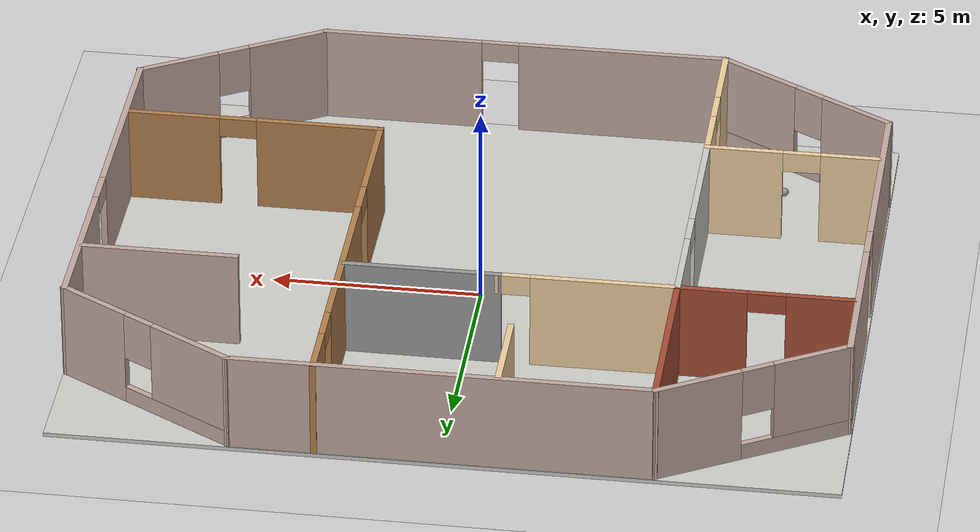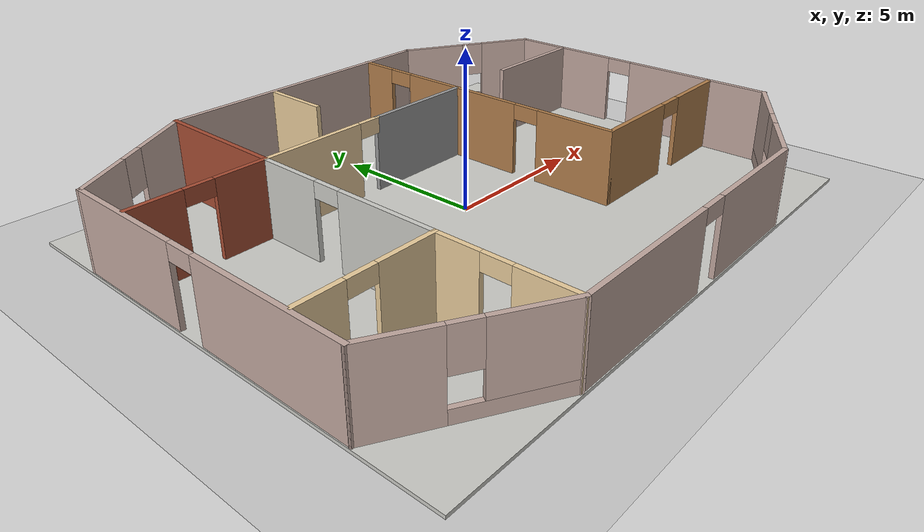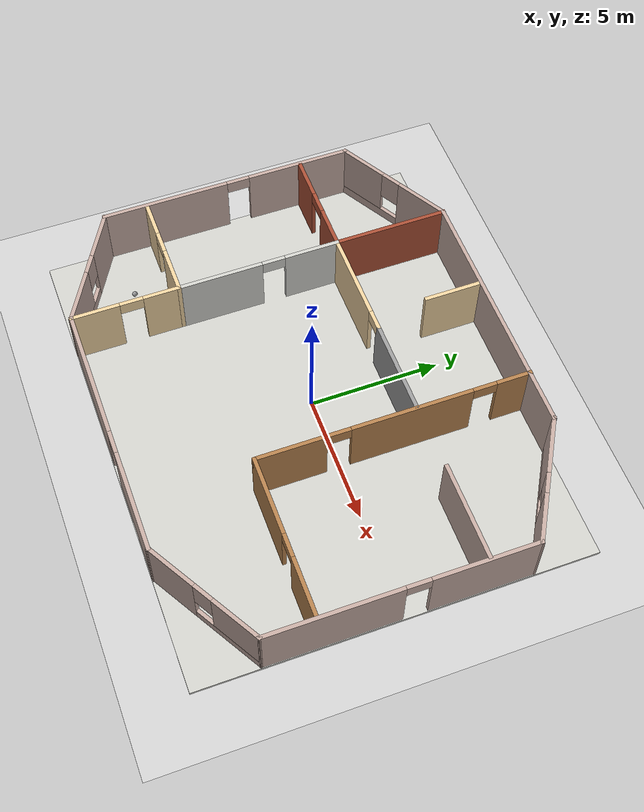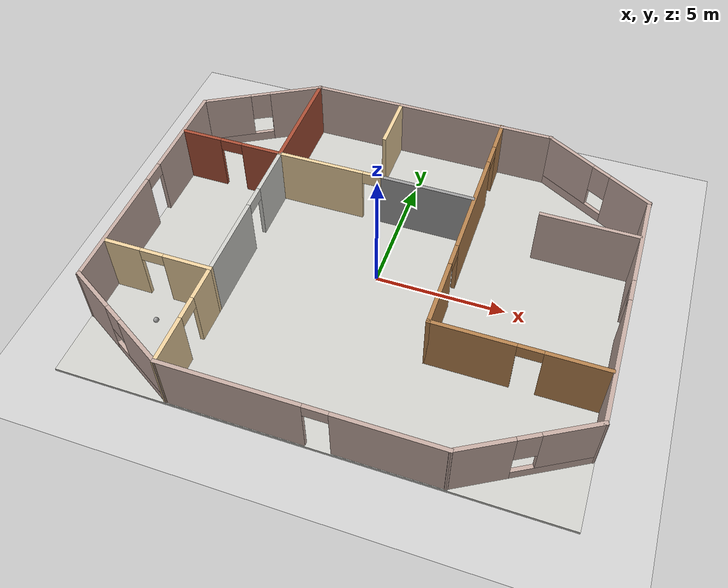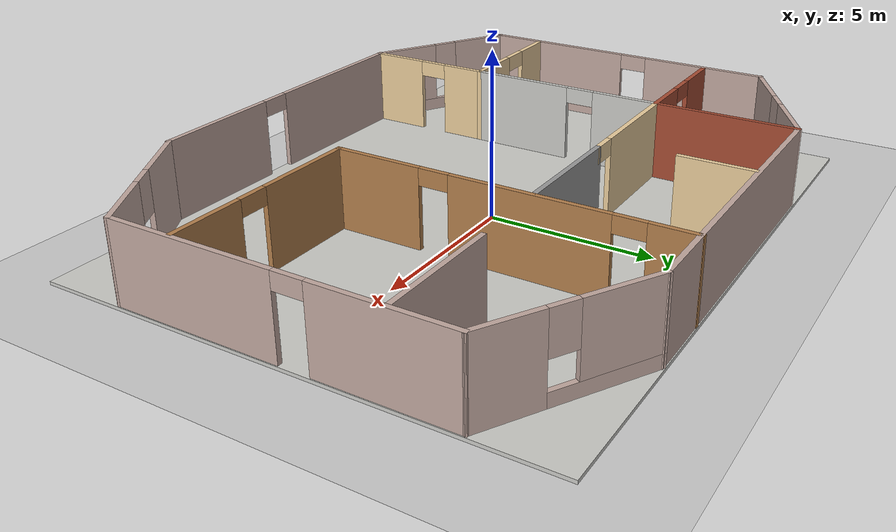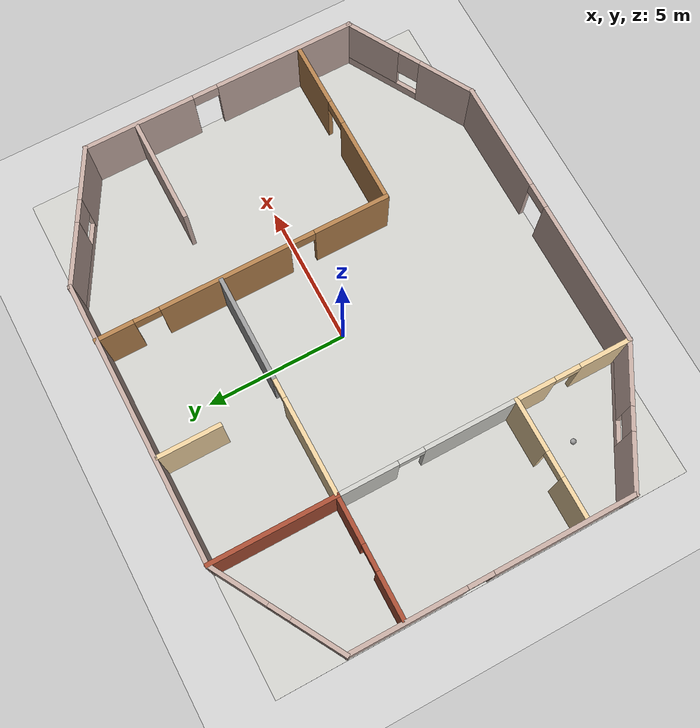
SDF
<sdf version="1.6">
 <world name="default">
  <light name="sun" type="directional">
   <pose>0 0 10 0 -0 0</pose>
   <diffuse>0.8 0.8 0.8 1</diffuse>
   <specular>0.1 0.1 0.1 1</specular>
   <attenuation>
    <range>1000</range>
    <constant>0.9</constant>
    <linear>0.01</linear>
    <quadratic>0.001</quadratic>
   </attenuation>
   <direction>-0.5 0.5 -1</direction>
  </light>
  <model name="ground_plane">
   <static>1</static>
   <link name="link">
    <collision name="collision">
     <geometry><plane><normal>0 0 1</normal><size>100 100</size></plane></geometry>
     <surface><friction><ode><mu>100</mu><mu2>50</mu2></ode></friction></surface>
    </collision>
    <visual name="visual">
     <cast_shadows>0</cast_shadows>
     <geometry><plane><normal>0 0 1</normal><size>100 100</size></plane></geometry>
     <material>
      <script><uri>file://media/materials/scripts/gazebo.material</uri><name>Gazebo/Grey</name></script>
     </material>
    </visual>
   </link>
  </model>
  <gravity>0 0 -9.8</gravity>
  <magnetic_field>6e-06 2.3e-05 -4.2e-05</magnetic_field>
  <atmosphere type="adiabatic"/>
  <physics name="default_physics" default="0" type="ode">
   <max_step_size>0.001</max_step_size>
   <real_time_factor>1</real_time_factor>
   <real_time_update_rate>1000</real_time_update_rate>
  </physics>
  <scene><ambient>0.4 0.4 0.4 1</ambient><background>0.7 0.7 0.7 1</background><shadows>1</shadows></scene>
  <spherical_coordinates>
   <surface_model>EARTH_WGS84</surface_model>
   <latitude_deg>0</latitude_deg>
   <longitude_deg>0</longitude_deg>
   <elevation>0</elevation>
   <heading_deg>0</heading_deg>
  </spherical_coordinates>
  <model name="new_floor">
   <link name="Floor_16">
    <pose>1e-06 0 0 0 -0 0</pose>
    <inertial>
     <mass>1</mass>
     <inertia><ixx>1</ixx><ixy>0</ixy><ixz>0</ixz><iyy>1</iyy><iyz>0</iyz><izz>1</izz></inertia>
    </inertial>
    <visual name="Floor_16_Visual">
     <pose>0 0 0.05 0 -0 0</pose>
     <geometry><box><size>18.4553 14.9049 0.1</size></box></geometry>
     <material>
      <script><uri>file://media/materials/scripts/gazebo.material</uri><name>Gazebo/CeilingTiled</name></script>
      <ambient>0.5 0.5 0.5 1</ambient>
      <shader type="pixel"><normal_map>__default__</normal_map></shader>
      <diffuse>0.5 0.5 0.5 1</diffuse>
      <specular>0 0 0 1</specular>
      <emissive>0 0 0 1</emissive>
     </material>
    </visual>
    <collision name="Floor_16_Collision">
     <pose>0 0 0.05 0 -0 0</pose>
     <geometry><box><size>18.4553 14.9049 0.1</size></box></geometry>
     <surface>
      <friction>
       <ode><mu>1</mu><mu2>1</mu2><fdir1>0 0 0</fdir1><slip1>0</slip1><slip2>0</slip2></ode>
       <torsional>
        <coefficient>1</coefficient>
        <patch_radius>0</patch_radius>
        <surface_radius>0</surface_radius>
        <use_patch_radius>1</use_patch_radius>
        <ode><slip>0</slip></ode>
       </torsional>
      </friction>
      <bounce><restitution_coefficient>0</restitution_coefficient><threshold>1e+06</threshold></bounce>
      <contact>
       <collide_without_contact>0</collide_without_contact>
       <collide_without_contact_bitmask>1</collide_without_contact_bitmask>
       <collide_bitmask>1</collide_bitmask>
       <ode>
        <soft_cfm>0</soft_cfm>
        <soft_erp>0.2</soft_erp>
        <kp>1e+13</kp>
        <kd>1</kd>
        <max_vel>0.01</max_vel>
        <min_depth>0</min_depth>
       </ode>
       <bullet>
        <split_impulse>1</split_impulse>
        <split_impulse_penetration_threshold>-0.01</split_impulse_penetration_threshold>
        <soft_cfm>0</soft_cfm>
        <soft_erp>0.2</soft_erp>
        <kp>1e+13</kp>
        <kd>1</kd>
       </bullet>
      </contact>
     </surface>
    </collision>
   </link>
   <link name="Wall_22">
    <pose>-9.12522 0 0 0 0 -1.5708</pose>
    <visual name="Wall_22_Visual_0">
     <pose>-2.94929 0 1.25 0 -0 0</pose>
     <geometry><box><size>4.10142 0.15 2.5</size></box></geometry>
     <material>
      <script><uri>file://media/materials/scripts/gazebo.material</uri><name>Gazebo/Grey</name></script>
      <ambient>0.760784 0.662745 0.627451 1</ambient>
      <shader type="pixel"/>
      <diffuse>0.7 0.7 0.7 1</diffuse>
      <specular>0.01 0.01 0.01 1</specular>
      <emissive>0 0 0 1</emissive>
     </material>
    </visual>
    <visual name="Wall_22_Visual_1">
     <pose>2.50071 0 1.25 0 -0 0</pose>
     <geometry><box><size>4.99857 0.15 2.5</size></box></geometry>
     <material>
      <script><uri>file://media/materials/scripts/gazebo.material</uri><name>Gazebo/Grey</name></script>
      <ambient>0.760784 0.662745 0.627451 1</ambient>
      <shader type="pixel"/>
      <diffuse>0.7 0.7 0.7 1</diffuse>
      <specular>0.01 0.01 0.01 1</specular>
      <emissive>0 0 0 1</emissive>
     </material>
    </visual>
    <visual name="Wall_22_Visual_2">
     <pose>-0.448575 0 2.25 0 -0 0</pose>
     <geometry><box><size>0.9 0.15 0.5</size></box></geometry>
     <material>
      <script><uri>file://media/materials/scripts/gazebo.material</uri><name>Gazebo/Grey</name></script>
      <ambient>0.760784 0.662745 0.627451 1</ambient>
      <shader type="pixel"/>
      <diffuse>0.7 0.7 0.7 1</diffuse>
      <specular>0.01 0.01 0.01 1</specular>
      <emissive>0 0 0 1</emissive>
     </material>
    </visual>
    <collision name="Wall_22_Collision_0">
     <pose>-2.94929 0 1.25 0 -0 0</pose>
     <geometry><box><size>4.10142 0.15 2.5</size></box></geometry>
     <surface>
      <friction>
       <ode><mu>1</mu><mu2>1</mu2><fdir1>0 0 0</fdir1><slip1>0</slip1><slip2>0</slip2></ode>
       <torsional>
        <coefficient>1</coefficient>
        <patch_radius>0</patch_radius>
        <surface_radius>0</surface_radius>
        <use_patch_radius>1</use_patch_radius>
        <ode><slip>0</slip></ode>
       </torsional>
      </friction>
      <bounce><restitution_coefficient>0</restitution_coefficient><threshold>1e+06</threshold></bounce>
      <contact>
       <collide_without_contact>0</collide_without_contact>
       <collide_without_contact_bitmask>1</collide_without_contact_bitmask>
       <collide_bitmask>1</collide_bitmask>
       <ode>
        <soft_cfm>0</soft_cfm>
        <soft_erp>0.2</soft_erp>
        <kp>1e+13</kp>
        <kd>1</kd>
        <max_vel>0.01</max_vel>
        <min_depth>0</min_depth>
       </ode>
       <bullet>
        <split_impulse>1</split_impulse>
        <split_impulse_penetration_threshold>-0.01</split_impulse_penetration_threshold>
        <soft_cfm>0</soft_cfm>
        <soft_erp>0.2</soft_erp>
        <kp>1e+13</kp>
        <kd>1</kd>
       </bullet>
      </contact>
     </surface>
    </collision>
    <collision name="Wall_22_Collision_2">
     <pose>-0.448575 0 2.25 0 -0 0</pose>
     <geometry><box><size>0.9 0.15 0.5</size></box></geometry>
     <surface>
      <friction>
       <ode><mu>1</mu><mu2>1</mu2><fdir1>0 0 0</fdir1><slip1>0</slip1><slip2>0</slip2></ode>
       <torsional>
        <coefficient>1</coefficient>
        <patch_radius>0</patch_radius>
        <surface_radius>0</surface_radius>
        <use_patch_radius>1</use_patch_radius>
        <ode><slip>0</slip></ode>
       </torsional>
      </friction>
      <bounce><restitution_coefficient>0</restitution_coefficient><threshold>1e+06</threshold></bounce>
      <contact>
       <collide_without_contact>0</collide_without_contact>
       <collide_without_contact_bitmask>1</collide_without_contact_bitmask>
       <collide_bitmask>1</collide_bitmask>
       <ode>
        <soft_cfm>0</soft_cfm>
        <soft_erp>0.2</soft_erp>
        <kp>1e+13</kp>
        <kd>1</kd>
        <max_vel>0.01</max_vel>
        <min_depth>0</min_depth>
       </ode>
       <bullet>
        <split_impulse>1</split_impulse>
        <split_impulse_penetration_threshold>-0.01</split_impulse_penetration_threshold>
        <soft_cfm>0</soft_cfm>
        <soft_erp>0.2</soft_erp>
        <kp>1e+13</kp>
        <kd>1</kd>
       </bullet>
      </contact>
     </surface>
    </collision>
    <collision name="Wall_22_Collision_1">
     <pose>2.50071 0 1.25 0 -0 0</pose>
     <geometry><box><size>4.99857 0.15 2.5</size></box></geometry>
     <surface>
      <friction>
       <ode><mu>1</mu><mu2>1</mu2><fdir1>0 0 0</fdir1><slip1>0</slip1><slip2>0</slip2></ode>
       <torsional>
        <coefficient>1</coefficient>
        <patch_radius>0</patch_radius>
        <surface_radius>0</surface_radius>
        <use_patch_radius>1</use_patch_radius>
        <ode><slip>0</slip></ode>
       </torsional>
      </friction>
      <bounce><restitution_coefficient>0</restitution_coefficient><threshold>1e+06</threshold></bounce>
      <contact>
       <collide_without_contact>0</collide_without_contact>
       <collide_without_contact_bitmask>1</collide_without_contact_bitmask>
       <collide_bitmask>1</collide_bitmask>
       <ode>
        <soft_cfm>0</soft_cfm>
        <soft_erp>0.2</soft_erp>
        <kp>1e+13</kp>
        <kd>1</kd>
        <max_vel>0.01</max_vel>
        <min_depth>0</min_depth>
       </ode>
       <bullet>
        <split_impulse>1</split_impulse>
        <split_impulse_penetration_threshold>-0.01</split_impulse_penetration_threshold>
        <soft_cfm>0</soft_cfm>
        <soft_erp>0.2</soft_erp>
        <kp>1e+13</kp>
        <kd>1</kd>
       </bullet>
      </contact>
     </surface>
    </collision>
   </link>
   <link name="Wall_24">
    <pose>-7.02511 -6.1375 0 0 0 -0.523599</pose>
    <visual name="Wall_24_Visual_0">
     <pose>-1.50611 0 1.25 0 -0 0</pose>
     <geometry><box><size>1.98778 0.15 2.5</size></box></geometry>
     <material>
      <script><uri>file://media/materials/scripts/gazebo.material</uri><name>Gazebo/Grey</name></script>
      <ambient>0.760784 0.662745 0.627451 1</ambient>
      <shader type="pixel"/>
      <diffuse>0.7 0.7 0.7 1</diffuse>
      <specular>0.01 0.01 0.01 1</specular>
      <emissive>0 0 0 1</emissive>
     </material>
    </visual>
    <visual name="Wall_24_Visual_1">
     <pose>0.993891 0 0.25 0 -0 0</pose>
     <geometry><box><size>3.01222 0.15 0.5</size></box></geometry>
     <material>
      <script><uri>file://media/materials/scripts/gazebo.material</uri><name>Gazebo/Grey</name></script>
      <ambient>0.760784 0.662745 0.627451 1</ambient>
      <shader type="pixel"/>
      <diffuse>0.7 0.7 0.7 1</diffuse>
      <specular>0.01 0.01 0.01 1</specular>
      <emissive>0 0 0 1</emissive>
     </material>
    </visual>
    <visual name="Wall_24_Visual_2">
     <pose>1.39389 0 1.5 0 -0 0</pose>
     <geometry><box><size>2.21222 0.15 2</size></box></geometry>
     <material>
      <script><uri>file://media/materials/scripts/gazebo.material</uri><name>Gazebo/Grey</name></script>
      <ambient>0.760784 0.662745 0.627451 1</ambient>
      <shader type="pixel"/>
      <diffuse>0.7 0.7 0.7 1</diffuse>
      <specular>0.01 0.01 0.01 1</specular>
      <emissive>0 0 0 1</emissive>
     </material>
    </visual>
    <visual name="Wall_24_Visual_3">
     <pose>-0.112218 0 1.9 0 -0 0</pose>
     <geometry><box><size>0.8 0.15 1.2</size></box></geometry>
     <material>
      <script><uri>file://media/materials/scripts/gazebo.material</uri><name>Gazebo/Grey</name></script>
      <ambient>0.760784 0.662745 0.627451 1</ambient>
      <shader type="pixel"/>
      <diffuse>0.7 0.7 0.7 1</diffuse>
      <specular>0.01 0.01 0.01 1</specular>
      <emissive>0 0 0 1</emissive>
     </material>
    </visual>
    <collision name="Wall_24_Collision_0">
     <pose>-1.50611 0 1.25 0 -0 0</pose>
     <geometry><box><size>1.98778 0.15 2.5</size></box></geometry>
     <surface>
      <friction>
       <ode><mu>1</mu><mu2>1</mu2><fdir1>0 0 0</fdir1><slip1>0</slip1><slip2>0</slip2></ode>
       <torsional>
        <coefficient>1</coefficient>
        <patch_radius>0</patch_radius>
        <surface_radius>0</surface_radius>
        <use_patch_radius>1</use_patch_radius>
        <ode><slip>0</slip></ode>
       </torsional>
      </friction>
      <bounce><restitution_coefficient>0</restitution_coefficient><threshold>1e+06</threshold></bounce>
      <contact>
       <collide_without_contact>0</collide_without_contact>
       <collide_without_contact_bitmask>1</collide_without_contact_bitmask>
       <collide_bitmask>1</collide_bitmask>
       <ode>
        <soft_cfm>0</soft_cfm>
        <soft_erp>0.2</soft_erp>
        <kp>1e+13</kp>
        <kd>1</kd>
        <max_vel>0.01</max_vel>
        <min_depth>0</min_depth>
       </ode>
       <bullet>
        <split_impulse>1</split_impulse>
        <split_impulse_penetration_threshold>-0.01</split_impulse_penetration_threshold>
        <soft_cfm>0</soft_cfm>
        <soft_erp>0.2</soft_erp>
        <kp>1e+13</kp>
        <kd>1</kd>
       </bullet>
      </contact>
     </surface>
    </collision>
    <collision name="Wall_24_Collision_1">
     <pose>0.993891 0 0.25 0 -0 0</pose>
     <geometry><box><size>3.01222 0.15 0.5</size></box></geometry>
     <surface>
      <friction>
       <ode><mu>1</mu><mu2>1</mu2><fdir1>0 0 0</fdir1><slip1>0</slip1><slip2>0</slip2></ode>
       <torsional>
        <coefficient>1</coefficient>
        <patch_radius>0</patch_radius>
        <surface_radius>0</surface_radius>
        <use_patch_radius>1</use_patch_radius>
        <ode><slip>0</slip></ode>
       </torsional>
      </friction>
      <bounce><restitution_coefficient>0</restitution_coefficient><threshold>1e+06</threshold></bounce>
      <contact>
       <collide_without_contact>0</collide_without_contact>
       <collide_without_contact_bitmask>1</collide_without_contact_bitmask>
       <collide_bitmask>1</collide_bitmask>
       <ode>
        <soft_cfm>0</soft_cfm>
        <soft_erp>0.2</soft_erp>
        <kp>1e+13</kp>
        <kd>1</kd>
        <max_vel>0.01</max_vel>
        <min_depth>0</min_depth>
       </ode>
       <bullet>
        <split_impulse>1</split_impulse>
        <split_impulse_penetration_threshold>-0.01</split_impulse_penetration_threshold>
        <soft_cfm>0</soft_cfm>
        <soft_erp>0.2</soft_erp>
        <kp>1e+13</kp>
        <kd>1</kd>
       </bullet>
      </contact>
     </surface>
    </collision>
    <collision name="Wall_24_Collision_2">
     <pose>1.39389 0 1.5 0 -0 0</pose>
     <geometry><box><size>2.21222 0.15 2</size></box></geometry>
     <surface>
      <friction>
       <ode><mu>1</mu><mu2>1</mu2><fdir1>0 0 0</fdir1><slip1>0</slip1><slip2>0</slip2></ode>
       <torsional>
        <coefficient>1</coefficient>
        <patch_radius>0</patch_radius>
        <surface_radius>0</surface_radius>
        <use_patch_radius>1</use_patch_radius>
        <ode><slip>0</slip></ode>
       </torsional>
      </friction>
      <bounce><restitution_coefficient>0</restitution_coefficient><threshold>1e+06</threshold></bounce>
      <contact>
       <collide_without_contact>0</collide_without_contact>
       <collide_without_contact_bitmask>1</collide_without_contact_bitmask>
       <collide_bitmask>1</collide_bitmask>
       <ode>
        <soft_cfm>0</soft_cfm>
        <soft_erp>0.2</soft_erp>
        <kp>1e+13</kp>
        <kd>1</kd>
        <max_vel>0.01</max_vel>
        <min_depth>0</min_depth>
       </ode>
       <bullet>
        <split_impulse>1</split_impulse>
        <split_impulse_penetration_threshold>-0.01</split_impulse_penetration_threshold>
        <soft_cfm>0</soft_cfm>
        <soft_erp>0.2</soft_erp>
        <kp>1e+13</kp>
        <kd>1</kd>
       </bullet>
      </contact>
     </surface>
    </collision>
    <collision name="Wall_24_Collision_3">
     <pose>-0.112218 0 1.9 0 -0 0</pose>
     <geometry><box><size>0.8 0.15 1.2</size></box></geometry>
     <surface>
      <friction>
       <ode><mu>1</mu><mu2>1</mu2><fdir1>0 0 0</fdir1><slip1>0</slip1><slip2>0</slip2></ode>
       <torsional>
        <coefficient>1</coefficient>
        <patch_radius>0</patch_radius>
        <surface_radius>0</surface_radius>
        <use_patch_radius>1</use_patch_radius>
        <ode><slip>0</slip></ode>
       </torsional>
      </friction>
      <bounce><restitution_coefficient>0</restitution_coefficient><threshold>1e+06</threshold></bounce>
      <contact>
       <collide_without_contact>0</collide_without_contact>
       <collide_without_contact_bitmask>1</collide_without_contact_bitmask>
       <collide_bitmask>1</collide_bitmask>
       <ode>
        <soft_cfm>0</soft_cfm>
        <soft_erp>0.2</soft_erp>
        <kp>1e+13</kp>
        <kd>1</kd>
        <max_vel>0.01</max_vel>
        <min_depth>0</min_depth>
       </ode>
       <bullet>
        <split_impulse>1</split_impulse>
        <split_impulse_penetration_threshold>-0.01</split_impulse_penetration_threshold>
        <soft_cfm>0</soft_cfm>
        <soft_erp>0.2</soft_erp>
        <kp>1e+13</kp>
        <kd>1</kd>
       </bullet>
      </contact>
     </surface>
    </collision>
   </link>
   <link name="Wall_25">
    <pose>1e-06 -7.35 0 0 -0 0</pose>
    <visual name="Wall_25_Visual_0">
     <pose>-2.41987 0 1.25 0 -0 0</pose>
     <geometry><box><size>5.16027 0.15 2.5</size></box></geometry>
     <material>
      <script><uri>file://media/materials/scripts/gazebo.material</uri><name>Gazebo/Grey</name></script>
      <ambient>0.760784 0.662745 0.627451 1</ambient>
      <shader type="pixel"/>
      <diffuse>0.7 0.7 0.7 1</diffuse>
      <specular>0.01 0.01 0.01 1</specular>
      <emissive>0 0 0 1</emissive>
     </material>
    </visual>
    <visual name="Wall_25_Visual_1">
     <pose>3.03013 0 1.25 0 -0 0</pose>
     <geometry><box><size>3.93973 0.15 2.5</size></box></geometry>
     <material>
      <script><uri>file://media/materials/scripts/gazebo.material</uri><name>Gazebo/Grey</name></script>
      <ambient>0.760784 0.662745 0.627451 1</ambient>
      <shader type="pixel"/>
      <diffuse>0.7 0.7 0.7 1</diffuse>
      <specular>0.01 0.01 0.01 1</specular>
      <emissive>0 0 0 1</emissive>
     </material>
    </visual>
    <visual name="Wall_25_Visual_2">
     <pose>0.610269 0 2.25 0 -0 0</pose>
     <geometry><box><size>0.9 0.15 0.5</size></box></geometry>
     <material>
      <script><uri>file://media/materials/scripts/gazebo.material</uri><name>Gazebo/Grey</name></script>
      <ambient>0.760784 0.662745 0.627451 1</ambient>
      <shader type="pixel"/>
      <diffuse>0.7 0.7 0.7 1</diffuse>
      <specular>0.01 0.01 0.01 1</specular>
      <emissive>0 0 0 1</emissive>
     </material>
    </visual>
    <collision name="Wall_25_Collision_0">
     <pose>-2.41987 0 1.25 0 -0 0</pose>
     <geometry><box><size>5.16027 0.15 2.5</size></box></geometry>
     <surface>
      <friction>
       <ode><mu>1</mu><mu2>1</mu2><fdir1>0 0 0</fdir1><slip1>0</slip1><slip2>0</slip2></ode>
       <torsional>
        <coefficient>1</coefficient>
        <patch_radius>0</patch_radius>
        <surface_radius>0</surface_radius>
        <use_patch_radius>1</use_patch_radius>
        <ode><slip>0</slip></ode>
       </torsional>
      </friction>
      <bounce><restitution_coefficient>0</restitution_coefficient><threshold>1e+06</threshold></bounce>
      <contact>
       <collide_without_contact>0</collide_without_contact>
       <collide_without_contact_bitmask>1</collide_without_contact_bitmask>
       <collide_bitmask>1</collide_bitmask>
       <ode>
        <soft_cfm>0</soft_cfm>
        <soft_erp>0.2</soft_erp>
        <kp>1e+13</kp>
        <kd>1</kd>
        <max_vel>0.01</max_vel>
        <min_depth>0</min_depth>
       </ode>
       <bullet>
        <split_impulse>1</split_impulse>
        <split_impulse_penetration_threshold>-0.01</split_impulse_penetration_threshold>
        <soft_cfm>0</soft_cfm>
        <soft_erp>0.2</soft_erp>
        <kp>1e+13</kp>
        <kd>1</kd>
       </bullet>
      </contact>
     </surface>
    </collision>
    <collision name="Wall_25_Collision_1">
     <pose>3.03013 0 1.25 0 -0 0</pose>
     <geometry><box><size>3.93973 0.15 2.5</size></box></geometry>
     <surface>
      <friction>
       <ode><mu>1</mu><mu2>1</mu2><fdir1>0 0 0</fdir1><slip1>0</slip1><slip2>0</slip2></ode>
       <torsional>
        <coefficient>1</coefficient>
        <patch_radius>0</patch_radius>
        <surface_radius>0</surface_radius>
        <use_patch_radius>1</use_patch_radius>
        <ode><slip>0</slip></ode>
       </torsional>
      </friction>
      <bounce><restitution_coefficient>0</restitution_coefficient><threshold>1e+06</threshold></bounce>
      <contact>
       <collide_without_contact>0</collide_without_contact>
       <collide_without_contact_bitmask>1</collide_without_contact_bitmask>
       <collide_bitmask>1</collide_bitmask>
       <ode>
        <soft_cfm>0</soft_cfm>
        <soft_erp>0.2</soft_erp>
        <kp>1e+13</kp>
        <kd>1</kd>
        <max_vel>0.01</max_vel>
        <min_depth>0</min_depth>
       </ode>
       <bullet>
        <split_impulse>1</split_impulse>
        <split_impulse_penetration_threshold>-0.01</split_impulse_penetration_threshold>
        <soft_cfm>0</soft_cfm>
        <soft_erp>0.2</soft_erp>
        <kp>1e+13</kp>
        <kd>1</kd>
       </bullet>
      </contact>
     </surface>
    </collision>
    <collision name="Wall_25_Collision_2">
     <pose>0.610269 0 2.25 0 -0 0</pose>
     <geometry><box><size>0.9 0.15 0.5</size></box></geometry>
     <surface>
      <friction>
       <ode><mu>1</mu><mu2>1</mu2><fdir1>0 0 0</fdir1><slip1>0</slip1><slip2>0</slip2></ode>
       <torsional>
        <coefficient>1</coefficient>
        <patch_radius>0</patch_radius>
        <surface_radius>0</surface_radius>
        <use_patch_radius>1</use_patch_radius>
        <ode><slip>0</slip></ode>
       </torsional>
      </friction>
      <bounce><restitution_coefficient>0</restitution_coefficient><threshold>1e+06</threshold></bounce>
      <contact>
       <collide_without_contact>0</collide_without_contact>
       <collide_without_contact_bitmask>1</collide_without_contact_bitmask>
       <collide_bitmask>1</collide_bitmask>
       <ode>
        <soft_cfm>0</soft_cfm>
        <soft_erp>0.2</soft_erp>
        <kp>1e+13</kp>
        <kd>1</kd>
        <max_vel>0.01</max_vel>
        <min_depth>0</min_depth>
       </ode>
       <bullet>
        <split_impulse>1</split_impulse>
        <split_impulse_penetration_threshold>-0.01</split_impulse_penetration_threshold>
        <soft_cfm>0</soft_cfm>
        <soft_erp>0.2</soft_erp>
        <kp>1e+13</kp>
        <kd>1</kd>
       </bullet>
      </contact>
     </surface>
    </collision>
   </link>
   <link name="Wall_26">
    <pose>7.02511 -6.1375 0 0 -0 0.523599</pose>
    <visual name="Wall_26_Visual_0">
     <pose>-1.44732 0 1.25 0 -0 0</pose>
     <geometry><box><size>2.10536 0.15 2.5</size></box></geometry>
     <material>
      <script><uri>file://media/materials/scripts/gazebo.material</uri><name>Gazebo/Grey</name></script>
      <ambient>0.760784 0.662745 0.627451 1</ambient>
      <shader type="pixel"/>
      <diffuse>0.7 0.7 0.7 1</diffuse>
      <specular>0.01 0.01 0.01 1</specular>
      <emissive>0 0 0 1</emissive>
     </material>
    </visual>
    <visual name="Wall_26_Visual_1">
     <pose>1.05268 0 0.25 0 -0 0</pose>
     <geometry><box><size>2.89464 0.15 0.5</size></box></geometry>
     <material>
      <script><uri>file://media/materials/scripts/gazebo.material</uri><name>Gazebo/Grey</name></script>
      <ambient>0.760784 0.662745 0.627451 1</ambient>
      <shader type="pixel"/>
      <diffuse>0.7 0.7 0.7 1</diffuse>
      <specular>0.01 0.01 0.01 1</specular>
      <emissive>0 0 0 1</emissive>
     </material>
    </visual>
    <visual name="Wall_26_Visual_2">
     <pose>1.45268 0 1.5 0 -0 0</pose>
     <geometry><box><size>2.09464 0.15 2</size></box></geometry>
     <material>
      <script><uri>file://media/materials/scripts/gazebo.material</uri><name>Gazebo/Grey</name></script>
      <ambient>0.760784 0.662745 0.627451 1</ambient>
      <shader type="pixel"/>
      <diffuse>0.7 0.7 0.7 1</diffuse>
      <specular>0.01 0.01 0.01 1</specular>
      <emissive>0 0 0 1</emissive>
     </material>
    </visual>
    <visual name="Wall_26_Visual_3">
     <pose>0.005362 0 1.9 0 -0 0</pose>
     <geometry><box><size>0.8 0.15 1.2</size></box></geometry>
     <material>
      <script><uri>file://media/materials/scripts/gazebo.material</uri><name>Gazebo/Grey</name></script>
      <ambient>0.760784 0.662745 0.627451 1</ambient>
      <shader type="pixel"/>
      <diffuse>0.7 0.7 0.7 1</diffuse>
      <specular>0.01 0.01 0.01 1</specular>
      <emissive>0 0 0 1</emissive>
     </material>
    </visual>
    <collision name="Wall_26_Collision_0">
     <pose>-1.44732 0 1.25 0 -0 0</pose>
     <geometry><box><size>2.10536 0.15 2.5</size></box></geometry>
     <surface>
      <friction>
       <ode><mu>1</mu><mu2>1</mu2><fdir1>0 0 0</fdir1><slip1>0</slip1><slip2>0</slip2></ode>
       <torsional>
        <coefficient>1</coefficient>
        <patch_radius>0</patch_radius>
        <surface_radius>0</surface_radius>
        <use_patch_radius>1</use_patch_radius>
        <ode><slip>0</slip></ode>
       </torsional>
      </friction>
      <bounce><restitution_coefficient>0</restitution_coefficient><threshold>1e+06</threshold></bounce>
      <contact>
       <collide_without_contact>0</collide_without_contact>
       <collide_without_contact_bitmask>1</collide_without_contact_bitmask>
       <collide_bitmask>1</collide_bitmask>
       <ode>
        <soft_cfm>0</soft_cfm>
        <soft_erp>0.2</soft_erp>
        <kp>1e+13</kp>
        <kd>1</kd>
        <max_vel>0.01</max_vel>
        <min_depth>0</min_depth>
       </ode>
       <bullet>
        <split_impulse>1</split_impulse>
        <split_impulse_penetration_threshold>-0.01</split_impulse_penetration_threshold>
        <soft_cfm>0</soft_cfm>
        <soft_erp>0.2</soft_erp>
        <kp>1e+13</kp>
        <kd>1</kd>
       </bullet>
      </contact>
     </surface>
    </collision>
    <collision name="Wall_26_Collision_1">
     <pose>1.05268 0 0.25 0 -0 0</pose>
     <geometry><box><size>2.89464 0.15 0.5</size></box></geometry>
     <surface>
      <friction>
       <ode><mu>1</mu><mu2>1</mu2><fdir1>0 0 0</fdir1><slip1>0</slip1><slip2>0</slip2></ode>
       <torsional>
        <coefficient>1</coefficient>
        <patch_radius>0</patch_radius>
        <surface_radius>0</surface_radius>
        <use_patch_radius>1</use_patch_radius>
        <ode><slip>0</slip></ode>
       </torsional>
      </friction>
      <bounce><restitution_coefficient>0</restitution_coefficient><threshold>1e+06</threshold></bounce>
      <contact>
       <collide_without_contact>0</collide_without_contact>
       <collide_without_contact_bitmask>1</collide_without_contact_bitmask>
       <collide_bitmask>1</collide_bitmask>
       <ode>
        <soft_cfm>0</soft_cfm>
        <soft_erp>0.2</soft_erp>
        <kp>1e+13</kp>
        <kd>1</kd>
        <max_vel>0.01</max_vel>
        <min_depth>0</min_depth>
       </ode>
       <bullet>
        <split_impulse>1</split_impulse>
        <split_impulse_penetration_threshold>-0.01</split_impulse_penetration_threshold>
        <soft_cfm>0</soft_cfm>
        <soft_erp>0.2</soft_erp>
        <kp>1e+13</kp>
        <kd>1</kd>
       </bullet>
      </contact>
     </surface>
    </collision>
    <collision name="Wall_26_Collision_2">
     <pose>1.45268 0 1.5 0 -0 0</pose>
     <geometry><box><size>2.09464 0.15 2</size></box></geometry>
     <surface>
      <friction>
       <ode><mu>1</mu><mu2>1</mu2><fdir1>0 0 0</fdir1><slip1>0</slip1><slip2>0</slip2></ode>
       <torsional>
        <coefficient>1</coefficient>
        <patch_radius>0</patch_radius>
        <surface_radius>0</surface_radius>
        <use_patch_radius>1</use_patch_radius>
        <ode><slip>0</slip></ode>
       </torsional>
      </friction>
      <bounce><restitution_coefficient>0</restitution_coefficient><threshold>1e+06</threshold></bounce>
      <contact>
       <collide_without_contact>0</collide_without_contact>
       <collide_without_contact_bitmask>1</collide_without_contact_bitmask>
       <collide_bitmask>1</collide_bitmask>
       <ode>
        <soft_cfm>0</soft_cfm>
        <soft_erp>0.2</soft_erp>
        <kp>1e+13</kp>
        <kd>1</kd>
        <max_vel>0.01</max_vel>
        <min_depth>0</min_depth>
       </ode>
       <bullet>
        <split_impulse>1</split_impulse>
        <split_impulse_penetration_threshold>-0.01</split_impulse_penetration_threshold>
        <soft_cfm>0</soft_cfm>
        <soft_erp>0.2</soft_erp>
        <kp>1e+13</kp>
        <kd>1</kd>
       </bullet>
      </contact>
     </surface>
    </collision>
    <collision name="Wall_26_Collision_3">
     <pose>0.005362 0 1.9 0 -0 0</pose>
     <geometry><box><size>0.8 0.15 1.2</size></box></geometry>
     <surface>
      <friction>
       <ode><mu>1</mu><mu2>1</mu2><fdir1>0 0 0</fdir1><slip1>0</slip1><slip2>0</slip2></ode>
       <torsional>
        <coefficient>1</coefficient>
        <patch_radius>0</patch_radius>
        <surface_radius>0</surface_radius>
        <use_patch_radius>1</use_patch_radius>
        <ode><slip>0</slip></ode>
       </torsional>
      </friction>
      <bounce><restitution_coefficient>0</restitution_coefficient><threshold>1e+06</threshold></bounce>
      <contact>
       <collide_without_contact>0</collide_without_contact>
       <collide_without_contact_bitmask>1</collide_without_contact_bitmask>
       <collide_bitmask>1</collide_bitmask>
       <ode>
        <soft_cfm>0</soft_cfm>
        <soft_erp>0.2</soft_erp>
        <kp>1e+13</kp>
        <kd>1</kd>
        <max_vel>0.01</max_vel>
        <min_depth>0</min_depth>
       </ode>
       <bullet>
        <split_impulse>1</split_impulse>
        <split_impulse_penetration_threshold>-0.01</split_impulse_penetration_threshold>
        <soft_cfm>0</soft_cfm>
        <soft_erp>0.2</soft_erp>
        <kp>1e+13</kp>
        <kd>1</kd>
       </bullet>
      </contact>
     </surface>
    </collision>
   </link>
   <link name="Wall_27">
    <pose>9.12522 0 0 0 -0 1.5708</pose>
    <visual name="Wall_27_Visual_0">
     <pose>-2.45419 0 1.25 0 -0 0</pose>
     <geometry><box><size>5.09162 0.15 2.5</size></box></geometry>
     <material>
      <script><uri>file://media/materials/scripts/gazebo.material</uri><name>Gazebo/Grey</name></script>
      <ambient>0.760784 0.662745 0.627451 1</ambient>
      <shader type="pixel"/>
      <diffuse>0.7 0.7 0.7 1</diffuse>
      <specular>0.01 0.01 0.01 1</specular>
      <emissive>0 0 0 1</emissive>
     </material>
    </visual>
    <visual name="Wall_27_Visual_1">
     <pose>2.99581 0 1.25 0 -0 0</pose>
     <geometry><box><size>4.00838 0.15 2.5</size></box></geometry>
     <material>
      <script><uri>file://media/materials/scripts/gazebo.material</uri><name>Gazebo/Grey</name></script>
      <ambient>0.760784 0.662745 0.627451 1</ambient>
      <shader type="pixel"/>
      <diffuse>0.7 0.7 0.7 1</diffuse>
      <specular>0.01 0.01 0.01 1</specular>
      <emissive>0 0 0 1</emissive>
     </material>
    </visual>
    <visual name="Wall_27_Visual_2">
     <pose>0.541623 0 2.25 0 -0 0</pose>
     <geometry><box><size>0.9 0.15 0.5</size></box></geometry>
     <material>
      <script><uri>file://media/materials/scripts/gazebo.material</uri><name>Gazebo/Grey</name></script>
      <ambient>0.760784 0.662745 0.627451 1</ambient>
      <shader type="pixel"/>
      <diffuse>0.7 0.7 0.7 1</diffuse>
      <specular>0.01 0.01 0.01 1</specular>
      <emissive>0 0 0 1</emissive>
     </material>
    </visual>
    <collision name="Wall_27_Collision_0">
     <pose>-2.45419 0 1.25 0 -0 0</pose>
     <geometry><box><size>5.09162 0.15 2.5</size></box></geometry>
     <surface>
      <friction>
       <ode><mu>1</mu><mu2>1</mu2><fdir1>0 0 0</fdir1><slip1>0</slip1><slip2>0</slip2></ode>
       <torsional>
        <coefficient>1</coefficient>
        <patch_radius>0</patch_radius>
        <surface_radius>0</surface_radius>
        <use_patch_radius>1</use_patch_radius>
        <ode><slip>0</slip></ode>
       </torsional>
      </friction>
      <bounce><restitution_coefficient>0</restitution_coefficient><threshold>1e+06</threshold></bounce>
      <contact>
       <collide_without_contact>0</collide_without_contact>
       <collide_without_contact_bitmask>1</collide_without_contact_bitmask>
       <collide_bitmask>1</collide_bitmask>
       <ode>
        <soft_cfm>0</soft_cfm>
        <soft_erp>0.2</soft_erp>
        <kp>1e+13</kp>
        <kd>1</kd>
        <max_vel>0.01</max_vel>
        <min_depth>0</min_depth>
       </ode>
       <bullet>
        <split_impulse>1</split_impulse>
        <split_impulse_penetration_threshold>-0.01</split_impulse_penetration_threshold>
        <soft_cfm>0</soft_cfm>
        <soft_erp>0.2</soft_erp>
        <kp>1e+13</kp>
        <kd>1</kd>
       </bullet>
      </contact>
     </surface>
    </collision>
    <collision name="Wall_27_Collision_1">
     <pose>2.99581 0 1.25 0 -0 0</pose>
     <geometry><box><size>4.00838 0.15 2.5</size></box></geometry>
     <surface>
      <friction>
       <ode><mu>1</mu><mu2>1</mu2><fdir1>0 0 0</fdir1><slip1>0</slip1><slip2>0</slip2></ode>
       <torsional>
        <coefficient>1</coefficient>
        <patch_radius>0</patch_radius>
        <surface_radius>0</surface_radius>
        <use_patch_radius>1</use_patch_radius>
        <ode><slip>0</slip></ode>
       </torsional>
      </friction>
      <bounce><restitution_coefficient>0</restitution_coefficient><threshold>1e+06</threshold></bounce>
      <contact>
       <collide_without_contact>0</collide_without_contact>
       <collide_without_contact_bitmask>1</collide_without_contact_bitmask>
       <collide_bitmask>1</collide_bitmask>
       <ode>
        <soft_cfm>0</soft_cfm>
        <soft_erp>0.2</soft_erp>
        <kp>1e+13</kp>
        <kd>1</kd>
        <max_vel>0.01</max_vel>
        <min_depth>0</min_depth>
       </ode>
       <bullet>
        <split_impulse>1</split_impulse>
        <split_impulse_penetration_threshold>-0.01</split_impulse_penetration_threshold>
        <soft_cfm>0</soft_cfm>
        <soft_erp>0.2</soft_erp>
        <kp>1e+13</kp>
        <kd>1</kd>
       </bullet>
      </contact>
     </surface>
    </collision>
    <collision name="Wall_27_Collision_2">
     <pose>0.541623 0 2.25 0 -0 0</pose>
     <geometry><box><size>0.9 0.15 0.5</size></box></geometry>
     <surface>
      <friction>
       <ode><mu>1</mu><mu2>1</mu2><fdir1>0 0 0</fdir1><slip1>0</slip1><slip2>0</slip2></ode>
       <torsional>
        <coefficient>1</coefficient>
        <patch_radius>0</patch_radius>
        <surface_radius>0</surface_radius>
        <use_patch_radius>1</use_patch_radius>
        <ode><slip>0</slip></ode>
       </torsional>
      </friction>
      <bounce><restitution_coefficient>0</restitution_coefficient><threshold>1e+06</threshold></bounce>
      <contact>
       <collide_without_contact>0</collide_without_contact>
       <collide_without_contact_bitmask>1</collide_without_contact_bitmask>
       <collide_bitmask>1</collide_bitmask>
       <ode>
        <soft_cfm>0</soft_cfm>
        <soft_erp>0.2</soft_erp>
        <kp>1e+13</kp>
        <kd>1</kd>
        <max_vel>0.01</max_vel>
        <min_depth>0</min_depth>
       </ode>
       <bullet>
        <split_impulse>1</split_impulse>
        <split_impulse_penetration_threshold>-0.01</split_impulse_penetration_threshold>
        <soft_cfm>0</soft_cfm>
        <soft_erp>0.2</soft_erp>
        <kp>1e+13</kp>
        <kd>1</kd>
       </bullet>
      </contact>
     </surface>
    </collision>
   </link>
   <link name="Wall_28">
    <pose>7.02511 6.1375 0 0 -0 2.61799</pose>
    <visual name="Wall_28_Visual_2">
     <pose>1.36069 0 1.5 0 -0 0</pose>
     <geometry><box><size>2.27863 0.15 2</size></box></geometry>
     <material>
      <script><uri>file://media/materials/scripts/gazebo.material</uri><name>Gazebo/Grey</name></script>
      <ambient>0.760784 0.662745 0.627451 1</ambient>
      <shader type="pixel"/>
      <diffuse>0.7 0.7 0.7 1</diffuse>
      <specular>0.01 0.01 0.01 1</specular>
      <emissive>0 0 0 1</emissive>
     </material>
    </visual>
    <visual name="Wall_28_Visual_0">
     <pose>-1.53931 0 1.25 0 -0 0</pose>
     <geometry><box><size>1.92137 0.15 2.5</size></box></geometry>
     <material>
      <script><uri>file://media/materials/scripts/gazebo.material</uri><name>Gazebo/Grey</name></script>
      <ambient>0.760784 0.662745 0.627451 1</ambient>
      <shader type="pixel"/>
      <diffuse>0.7 0.7 0.7 1</diffuse>
      <specular>0.01 0.01 0.01 1</specular>
      <emissive>0 0 0 1</emissive>
     </material>
    </visual>
    <visual name="Wall_28_Visual_1">
     <pose>0.960687 0 0.25 0 -0 0</pose>
     <geometry><box><size>3.07863 0.15 0.5</size></box></geometry>
     <material>
      <script><uri>file://media/materials/scripts/gazebo.material</uri><name>Gazebo/Grey</name></script>
      <ambient>0.760784 0.662745 0.627451 1</ambient>
      <shader type="pixel"/>
      <diffuse>0.7 0.7 0.7 1</diffuse>
      <specular>0.01 0.01 0.01 1</specular>
      <emissive>0 0 0 1</emissive>
     </material>
    </visual>
    <visual name="Wall_28_Visual_3">
     <pose>-0.178626 0 1.9 0 -0 0</pose>
     <geometry><box><size>0.8 0.15 1.2</size></box></geometry>
     <material>
      <script><uri>file://media/materials/scripts/gazebo.material</uri><name>Gazebo/Grey</name></script>
      <ambient>0.760784 0.662745 0.627451 1</ambient>
      <shader type="pixel"/>
      <diffuse>0.7 0.7 0.7 1</diffuse>
      <specular>0.01 0.01 0.01 1</specular>
      <emissive>0 0 0 1</emissive>
     </material>
    </visual>
    <collision name="Wall_28_Collision_0">
     <pose>-1.53931 0 1.25 0 -0 0</pose>
     <geometry><box><size>1.92137 0.15 2.5</size></box></geometry>
     <surface>
      <friction>
       <ode><mu>1</mu><mu2>1</mu2><fdir1>0 0 0</fdir1><slip1>0</slip1><slip2>0</slip2></ode>
       <torsional>
        <coefficient>1</coefficient>
        <patch_radius>0</patch_radius>
        <surface_radius>0</surface_radius>
        <use_patch_radius>1</use_patch_radius>
        <ode><slip>0</slip></ode>
       </torsional>
      </friction>
      <bounce><restitution_coefficient>0</restitution_coefficient><threshold>1e+06</threshold></bounce>
      <contact>
       <collide_without_contact>0</collide_without_contact>
       <collide_without_contact_bitmask>1</collide_without_contact_bitmask>
       <collide_bitmask>1</collide_bitmask>
       <ode>
        <soft_cfm>0</soft_cfm>
        <soft_erp>0.2</soft_erp>
        <kp>1e+13</kp>
        <kd>1</kd>
        <max_vel>0.01</max_vel>
        <min_depth>0</min_depth>
       </ode>
       <bullet>
        <split_impulse>1</split_impulse>
        <split_impulse_penetration_threshold>-0.01</split_impulse_penetration_threshold>
        <soft_cfm>0</soft_cfm>
        <soft_erp>0.2</soft_erp>
        <kp>1e+13</kp>
        <kd>1</kd>
       </bullet>
      </contact>
     </surface>
    </collision>
    <collision name="Wall_28_Collision_1">
     <pose>0.960687 0 0.25 0 -0 0</pose>
     <geometry><box><size>3.07863 0.15 0.5</size></box></geometry>
     <surface>
      <friction>
       <ode><mu>1</mu><mu2>1</mu2><fdir1>0 0 0</fdir1><slip1>0</slip1><slip2>0</slip2></ode>
       <torsional>
        <coefficient>1</coefficient>
        <patch_radius>0</patch_radius>
        <surface_radius>0</surface_radius>
        <use_patch_radius>1</use_patch_radius>
        <ode><slip>0</slip></ode>
       </torsional>
      </friction>
      <bounce><restitution_coefficient>0</restitution_coefficient><threshold>1e+06</threshold></bounce>
      <contact>
       <collide_without_contact>0</collide_without_contact>
       <collide_without_contact_bitmask>1</collide_without_contact_bitmask>
       <collide_bitmask>1</collide_bitmask>
       <ode>
        <soft_cfm>0</soft_cfm>
        <soft_erp>0.2</soft_erp>
        <kp>1e+13</kp>
        <kd>1</kd>
        <max_vel>0.01</max_vel>
        <min_depth>0</min_depth>
       </ode>
       <bullet>
        <split_impulse>1</split_impulse>
        <split_impulse_penetration_threshold>-0.01</split_impulse_penetration_threshold>
        <soft_cfm>0</soft_cfm>
        <soft_erp>0.2</soft_erp>
        <kp>1e+13</kp>
        <kd>1</kd>
       </bullet>
      </contact>
     </surface>
    </collision>
    <collision name="Wall_28_Collision_2">
     <pose>1.36069 0 1.5 0 -0 0</pose>
     <geometry><box><size>2.27863 0.15 2</size></box></geometry>
     <surface>
      <friction>
       <ode><mu>1</mu><mu2>1</mu2><fdir1>0 0 0</fdir1><slip1>0</slip1><slip2>0</slip2></ode>
       <torsional>
        <coefficient>1</coefficient>
        <patch_radius>0</patch_radius>
        <surface_radius>0</surface_radius>
        <use_patch_radius>1</use_patch_radius>
        <ode><slip>0</slip></ode>
       </torsional>
      </friction>
      <bounce><restitution_coefficient>0</restitution_coefficient><threshold>1e+06</threshold></bounce>
      <contact>
       <collide_without_contact>0</collide_without_contact>
       <collide_without_contact_bitmask>1</collide_without_contact_bitmask>
       <collide_bitmask>1</collide_bitmask>
       <ode>
        <soft_cfm>0</soft_cfm>
        <soft_erp>0.2</soft_erp>
        <kp>1e+13</kp>
        <kd>1</kd>
        <max_vel>0.01</max_vel>
        <min_depth>0</min_depth>
       </ode>
       <bullet>
        <split_impulse>1</split_impulse>
        <split_impulse_penetration_threshold>-0.01</split_impulse_penetration_threshold>
        <soft_cfm>0</soft_cfm>
        <soft_erp>0.2</soft_erp>
        <kp>1e+13</kp>
        <kd>1</kd>
       </bullet>
      </contact>
     </surface>
    </collision>
    <collision name="Wall_28_Collision_3">
     <pose>-0.178626 0 1.9 0 -0 0</pose>
     <geometry><box><size>0.8 0.15 1.2</size></box></geometry>
     <surface>
      <friction>
       <ode><mu>1</mu><mu2>1</mu2><fdir1>0 0 0</fdir1><slip1>0</slip1><slip2>0</slip2></ode>
       <torsional>
        <coefficient>1</coefficient>
        <patch_radius>0</patch_radius>
        <surface_radius>0</surface_radius>
        <use_patch_radius>1</use_patch_radius>
        <ode><slip>0</slip></ode>
       </torsional>
      </friction>
      <bounce><restitution_coefficient>0</restitution_coefficient><threshold>1e+06</threshold></bounce>
      <contact>
       <collide_without_contact>0</collide_without_contact>
       <collide_without_contact_bitmask>1</collide_without_contact_bitmask>
       <collide_bitmask>1</collide_bitmask>
       <ode>
        <soft_cfm>0</soft_cfm>
        <soft_erp>0.2</soft_erp>
        <kp>1e+13</kp>
        <kd>1</kd>
        <max_vel>0.01</max_vel>
        <min_depth>0</min_depth>
       </ode>
       <bullet>
        <split_impulse>1</split_impulse>
        <split_impulse_penetration_threshold>-0.01</split_impulse_penetration_threshold>
        <soft_cfm>0</soft_cfm>
        <soft_erp>0.2</soft_erp>
        <kp>1e+13</kp>
        <kd>1</kd>
       </bullet>
      </contact>
     </surface>
    </collision>
   </link>
   <link name="Wall_29">
    <pose>1e-06 7.35 0 0 -0 3.14159</pose>
    <visual name="Wall_29_Visual">
     <pose>0 0 1.25 0 -0 0</pose>
     <geometry><box><size>10 0.15 2.5</size></box></geometry>
     <material>
      <script><uri>file://media/materials/scripts/gazebo.material</uri><name>Gazebo/Grey</name></script>
      <ambient>0.760784 0.662745 0.627451 1</ambient>
      <shader type="pixel"/>
      <diffuse>0.7 0.7 0.7 1</diffuse>
      <specular>0.01 0.01 0.01 1</specular>
      <emissive>0 0 0 1</emissive>
     </material>
    </visual>
    <collision name="Wall_29_Collision">
     <pose>0 0 1.25 0 -0 0</pose>
     <geometry><box><size>10 0.15 2.5</size></box></geometry>
     <surface>
      <friction>
       <ode><mu>1</mu><mu2>1</mu2><fdir1>0 0 0</fdir1><slip1>0</slip1><slip2>0</slip2></ode>
       <torsional>
        <coefficient>1</coefficient>
        <patch_radius>0</patch_radius>
        <surface_radius>0</surface_radius>
        <use_patch_radius>1</use_patch_radius>
        <ode><slip>0</slip></ode>
       </torsional>
      </friction>
      <bounce><restitution_coefficient>0</restitution_coefficient><threshold>1e+06</threshold></bounce>
      <contact>
       <collide_without_contact>0</collide_without_contact>
       <collide_without_contact_bitmask>1</collide_without_contact_bitmask>
       <collide_bitmask>1</collide_bitmask>
       <ode>
        <soft_cfm>0</soft_cfm>
        <soft_erp>0.2</soft_erp>
        <kp>1e+13</kp>
        <kd>1</kd>
        <max_vel>0.01</max_vel>
        <min_depth>0</min_depth>
       </ode>
       <bullet>
        <split_impulse>1</split_impulse>
        <split_impulse_penetration_threshold>-0.01</split_impulse_penetration_threshold>
        <soft_cfm>0</soft_cfm>
        <soft_erp>0.2</soft_erp>
        <kp>1e+13</kp>
        <kd>1</kd>
       </bullet>
      </contact>
     </surface>
    </collision>
   </link>
   <link name="Wall_30">
    <pose>-7.02511 6.1375 0 0 0 -2.61799</pose>
    <visual name="Wall_30_Visual_0">
     <pose>-1.39719 0 1.25 0 -0 0</pose>
     <geometry><box><size>2.20562 0.15 2.5</size></box></geometry>
     <material>
      <script><uri>file://media/materials/scripts/gazebo.material</uri><name>Gazebo/Grey</name></script>
      <ambient>0.760784 0.662745 0.627451 1</ambient>
      <shader type="pixel"/>
      <diffuse>0.7 0.7 0.7 1</diffuse>
      <specular>0.01 0.01 0.01 1</specular>
      <emissive>0 0 0 1</emissive>
     </material>
    </visual>
    <visual name="Wall_30_Visual_1">
     <pose>1.10281 0 0.25 0 -0 0</pose>
     <geometry><box><size>2.79438 0.15 0.5</size></box></geometry>
     <material>
      <script><uri>file://media/materials/scripts/gazebo.material</uri><name>Gazebo/Grey</name></script>
      <ambient>0.760784 0.662745 0.627451 1</ambient>
      <shader type="pixel"/>
      <diffuse>0.7 0.7 0.7 1</diffuse>
      <specular>0.01 0.01 0.01 1</specular>
      <emissive>0 0 0 1</emissive>
     </material>
    </visual>
    <visual name="Wall_30_Visual_2">
     <pose>1.50281 0 1.5 0 -0 0</pose>
     <geometry><box><size>1.99438 0.15 2</size></box></geometry>
     <material>
      <script><uri>file://media/materials/scripts/gazebo.material</uri><name>Gazebo/Grey</name></script>
      <ambient>0.760784 0.662745 0.627451 1</ambient>
      <shader type="pixel"/>
      <diffuse>0.7 0.7 0.7 1</diffuse>
      <specular>0.01 0.01 0.01 1</specular>
      <emissive>0 0 0 1</emissive>
     </material>
    </visual>
    <visual name="Wall_30_Visual_3">
     <pose>0.10562 0 1.9 0 -0 0</pose>
     <geometry><box><size>0.8 0.15 1.2</size></box></geometry>
     <material>
      <script><uri>file://media/materials/scripts/gazebo.material</uri><name>Gazebo/Grey</name></script>
      <ambient>0.760784 0.662745 0.627451 1</ambient>
      <shader type="pixel"/>
      <diffuse>0.7 0.7 0.7 1</diffuse>
      <specular>0.01 0.01 0.01 1</specular>
      <emissive>0 0 0 1</emissive>
     </material>
    </visual>
    <collision name="Wall_30_Collision_0">
     <pose>-1.39719 0 1.25 0 -0 0</pose>
     <geometry><box><size>2.20562 0.15 2.5</size></box></geometry>
     <surface>
      <friction>
       <ode><mu>1</mu><mu2>1</mu2><fdir1>0 0 0</fdir1><slip1>0</slip1><slip2>0</slip2></ode>
       <torsional>
        <coefficient>1</coefficient>
        <patch_radius>0</patch_radius>
        <surface_radius>0</surface_radius>
        <use_patch_radius>1</use_patch_radius>
        <ode><slip>0</slip></ode>
       </torsional>
      </friction>
      <bounce><restitution_coefficient>0</restitution_coefficient><threshold>1e+06</threshold></bounce>
      <contact>
       <collide_without_contact>0</collide_without_contact>
       <collide_without_contact_bitmask>1</collide_without_contact_bitmask>
       <collide_bitmask>1</collide_bitmask>
       <ode>
        <soft_cfm>0</soft_cfm>
        <soft_erp>0.2</soft_erp>
        <kp>1e+13</kp>
        <kd>1</kd>
        <max_vel>0.01</max_vel>
        <min_depth>0</min_depth>
       </ode>
       <bullet>
        <split_impulse>1</split_impulse>
        <split_impulse_penetration_threshold>-0.01</split_impulse_penetration_threshold>
        <soft_cfm>0</soft_cfm>
        <soft_erp>0.2</soft_erp>
        <kp>1e+13</kp>
        <kd>1</kd>
       </bullet>
      </contact>
     </surface>
    </collision>
    <collision name="Wall_30_Collision_1">
     <pose>1.10281 0 0.25 0 -0 0</pose>
     <geometry><box><size>2.79438 0.15 0.5</size></box></geometry>
     <surface>
      <friction>
       <ode><mu>1</mu><mu2>1</mu2><fdir1>0 0 0</fdir1><slip1>0</slip1><slip2>0</slip2></ode>
       <torsional>
        <coefficient>1</coefficient>
        <patch_radius>0</patch_radius>
        <surface_radius>0</surface_radius>
        <use_patch_radius>1</use_patch_radius>
        <ode><slip>0</slip></ode>
       </torsional>
      </friction>
      <bounce><restitution_coefficient>0</restitution_coefficient><threshold>1e+06</threshold></bounce>
      <contact>
       <collide_without_contact>0</collide_without_contact>
       <collide_without_contact_bitmask>1</collide_without_contact_bitmask>
       <collide_bitmask>1</collide_bitmask>
       <ode>
        <soft_cfm>0</soft_cfm>
        <soft_erp>0.2</soft_erp>
        <kp>1e+13</kp>
        <kd>1</kd>
        <max_vel>0.01</max_vel>
        <min_depth>0</min_depth>
       </ode>
       <bullet>
        <split_impulse>1</split_impulse>
        <split_impulse_penetration_threshold>-0.01</split_impulse_penetration_threshold>
        <soft_cfm>0</soft_cfm>
        <soft_erp>0.2</soft_erp>
        <kp>1e+13</kp>
        <kd>1</kd>
       </bullet>
      </contact>
     </surface>
    </collision>
    <collision name="Wall_30_Collision_2">
     <pose>1.50281 0 1.5 0 -0 0</pose>
     <geometry><box><size>1.99438 0.15 2</size></box></geometry>
     <surface>
      <friction>
       <ode><mu>1</mu><mu2>1</mu2><fdir1>0 0 0</fdir1><slip1>0</slip1><slip2>0</slip2></ode>
       <torsional>
        <coefficient>1</coefficient>
        <patch_radius>0</patch_radius>
        <surface_radius>0</surface_radius>
        <use_patch_radius>1</use_patch_radius>
        <ode><slip>0</slip></ode>
       </torsional>
      </friction>
      <bounce><restitution_coefficient>0</restitution_coefficient><threshold>1e+06</threshold></bounce>
      <contact>
       <collide_without_contact>0</collide_without_contact>
       <collide_without_contact_bitmask>1</collide_without_contact_bitmask>
       <collide_bitmask>1</collide_bitmask>
       <ode>
        <soft_cfm>0</soft_cfm>
        <soft_erp>0.2</soft_erp>
        <kp>1e+13</kp>
        <kd>1</kd>
        <max_vel>0.01</max_vel>
        <min_depth>0</min_depth>
       </ode>
       <bullet>
        <split_impulse>1</split_impulse>
        <split_impulse_penetration_threshold>-0.01</split_impulse_penetration_threshold>
        <soft_cfm>0</soft_cfm>
        <soft_erp>0.2</soft_erp>
        <kp>1e+13</kp>
        <kd>1</kd>
       </bullet>
      </contact>
     </surface>
    </collision>
    <collision name="Wall_30_Collision_3">
     <pose>0.10562 0 1.9 0 -0 0</pose>
     <geometry><box><size>0.8 0.15 1.2</size></box></geometry>
     <surface>
      <friction>
       <ode><mu>1</mu><mu2>1</mu2><fdir1>0 0 0</fdir1><slip1>0</slip1><slip2>0</slip2></ode>
       <torsional>
        <coefficient>1</coefficient>
        <patch_radius>0</patch_radius>
        <surface_radius>0</surface_radius>
        <use_patch_radius>1</use_patch_radius>
        <ode><slip>0</slip></ode>
       </torsional>
      </friction>
      <bounce><restitution_coefficient>0</restitution_coefficient><threshold>1e+06</threshold></bounce>
      <contact>
       <collide_without_contact>0</collide_without_contact>
       <collide_without_contact_bitmask>1</collide_without_contact_bitmask>
       <collide_bitmask>1</collide_bitmask>
       <ode>
        <soft_cfm>0</soft_cfm>
        <soft_erp>0.2</soft_erp>
        <kp>1e+13</kp>
        <kd>1</kd>
        <max_vel>0.01</max_vel>
        <min_depth>0</min_depth>
       </ode>
       <bullet>
        <split_impulse>1</split_impulse>
        <split_impulse_penetration_threshold>-0.01</split_impulse_penetration_threshold>
        <soft_cfm>0</soft_cfm>
        <soft_erp>0.2</soft_erp>
        <kp>1e+13</kp>
        <kd>1</kd>
       </bullet>
      </contact>
     </surface>
    </collision>
   </link>
   <link name="Wall_32">
    <pose>-4.925 5.175 0 0 0 -1.5708</pose>
    <visual name="Wall_32_Visual">
     <pose>0 0 1.25 0 -0 0</pose>
     <geometry><box><size>4.5 0.15 2.5</size></box></geometry>
     <material>
      <script><uri>file://media/materials/scripts/gazebo.material</uri><name>Gazebo/Bricks</name></script>
      <ambient>1 1 1 1</ambient>
      <shader type="pixel"/>
      <diffuse>1 1 1 1</diffuse>
      <specular>0.2 0.2 0.2 1</specular>
      <emissive>0 0 0 1</emissive>
     </material>
    </visual>
    <collision name="Wall_32_Collision">
     <pose>0 0 1.25 0 -0 0</pose>
     <geometry><box><size>4.5 0.15 2.5</size></box></geometry>
     <surface>
      <friction>
       <ode><mu>1</mu><mu2>1</mu2><fdir1>0 0 0</fdir1><slip1>0</slip1><slip2>0</slip2></ode>
       <torsional>
        <coefficient>1</coefficient>
        <patch_radius>0</patch_radius>
        <surface_radius>0</surface_radius>
        <use_patch_radius>1</use_patch_radius>
        <ode><slip>0</slip></ode>
       </torsional>
      </friction>
      <bounce><restitution_coefficient>0</restitution_coefficient><threshold>1e+06</threshold></bounce>
      <contact>
       <collide_without_contact>0</collide_without_contact>
       <collide_without_contact_bitmask>1</collide_without_contact_bitmask>
       <collide_bitmask>1</collide_bitmask>
       <ode>
        <soft_cfm>0</soft_cfm>
        <soft_erp>0.2</soft_erp>
        <kp>1e+13</kp>
        <kd>1</kd>
        <max_vel>0.01</max_vel>
        <min_depth>0</min_depth>
       </ode>
       <bullet>
        <split_impulse>1</split_impulse>
        <split_impulse_penetration_threshold>-0.01</split_impulse_penetration_threshold>
        <soft_cfm>0</soft_cfm>
        <soft_erp>0.2</soft_erp>
        <kp>1e+13</kp>
        <kd>1</kd>
       </bullet>
      </contact>
     </surface>
    </collision>
   </link>
   <link name="Wall_33">
    <pose>-6.975 3 0 0 -0 3.14159</pose>
    <visual name="Wall_33_Visual_0">
     <pose>-1.27049 0 1.25 0 -0 0</pose>
     <geometry><box><size>1.70902 0.15 2.5</size></box></geometry>
     <material>
      <script><uri>file://media/materials/scripts/gazebo.material</uri><name>Gazebo/Bricks</name></script>
      <ambient>1 1 1 1</ambient>
      <shader type="pixel"/>
      <diffuse>1 1 1 1</diffuse>
      <specular>0.2 0.2 0.2 1</specular>
      <emissive>0 0 0 1</emissive>
     </material>
    </visual>
    <visual name="Wall_33_Visual_1">
     <pose>1.30451 0 1.25 0 -0 0</pose>
     <geometry><box><size>1.64098 0.15 2.5</size></box></geometry>
     <material>
      <script><uri>file://media/materials/scripts/gazebo.material</uri><name>Gazebo/Bricks</name></script>
      <ambient>1 1 1 1</ambient>
      <shader type="pixel"/>
      <diffuse>1 1 1 1</diffuse>
      <specular>0.2 0.2 0.2 1</specular>
      <emissive>0 0 0 1</emissive>
     </material>
    </visual>
    <visual name="Wall_33_Visual_2">
     <pose>0.034019 0 2.25 0 -0 0</pose>
     <geometry><box><size>0.9 0.15 0.5</size></box></geometry>
     <material>
      <script><uri>file://media/materials/scripts/gazebo.material</uri><name>Gazebo/Bricks</name></script>
      <ambient>1 1 1 1</ambient>
      <shader type="pixel"/>
      <diffuse>1 1 1 1</diffuse>
      <specular>0.2 0.2 0.2 1</specular>
      <emissive>0 0 0 1</emissive>
     </material>
    </visual>
    <collision name="Wall_33_Collision_0">
     <pose>-1.27049 0 1.25 0 -0 0</pose>
     <geometry><box><size>1.70902 0.15 2.5</size></box></geometry>
     <surface>
      <friction>
       <ode><mu>1</mu><mu2>1</mu2><fdir1>0 0 0</fdir1><slip1>0</slip1><slip2>0</slip2></ode>
       <torsional>
        <coefficient>1</coefficient>
        <patch_radius>0</patch_radius>
        <surface_radius>0</surface_radius>
        <use_patch_radius>1</use_patch_radius>
        <ode><slip>0</slip></ode>
       </torsional>
      </friction>
      <bounce><restitution_coefficient>0</restitution_coefficient><threshold>1e+06</threshold></bounce>
      <contact>
       <collide_without_contact>0</collide_without_contact>
       <collide_without_contact_bitmask>1</collide_without_contact_bitmask>
       <collide_bitmask>1</collide_bitmask>
       <ode>
        <soft_cfm>0</soft_cfm>
        <soft_erp>0.2</soft_erp>
        <kp>1e+13</kp>
        <kd>1</kd>
        <max_vel>0.01</max_vel>
        <min_depth>0</min_depth>
       </ode>
       <bullet>
        <split_impulse>1</split_impulse>
        <split_impulse_penetration_threshold>-0.01</split_impulse_penetration_threshold>
        <soft_cfm>0</soft_cfm>
        <soft_erp>0.2</soft_erp>
        <kp>1e+13</kp>
        <kd>1</kd>
       </bullet>
      </contact>
     </surface>
    </collision>
    <collision name="Wall_33_Collision_1">
     <pose>1.30451 0 1.25 0 -0 0</pose>
     <geometry><box><size>1.64098 0.15 2.5</size></box></geometry>
     <surface>
      <friction>
       <ode><mu>1</mu><mu2>1</mu2><fdir1>0 0 0</fdir1><slip1>0</slip1><slip2>0</slip2></ode>
       <torsional>
        <coefficient>1</coefficient>
        <patch_radius>0</patch_radius>
        <surface_radius>0</surface_radius>
        <use_patch_radius>1</use_patch_radius>
        <ode><slip>0</slip></ode>
       </torsional>
      </friction>
      <bounce><restitution_coefficient>0</restitution_coefficient><threshold>1e+06</threshold></bounce>
      <contact>
       <collide_without_contact>0</collide_without_contact>
       <collide_without_contact_bitmask>1</collide_without_contact_bitmask>
       <collide_bitmask>1</collide_bitmask>
       <ode>
        <soft_cfm>0</soft_cfm>
        <soft_erp>0.2</soft_erp>
        <kp>1e+13</kp>
        <kd>1</kd>
        <max_vel>0.01</max_vel>
        <min_depth>0</min_depth>
       </ode>
       <bullet>
        <split_impulse>1</split_impulse>
        <split_impulse_penetration_threshold>-0.01</split_impulse_penetration_threshold>
        <soft_cfm>0</soft_cfm>
        <soft_erp>0.2</soft_erp>
        <kp>1e+13</kp>
        <kd>1</kd>
       </bullet>
      </contact>
     </surface>
    </collision>
    <collision name="Wall_33_Collision_2">
     <pose>0.034019 0 2.25 0 -0 0</pose>
     <geometry><box><size>0.9 0.15 0.5</size></box></geometry>
     <surface>
      <friction>
       <ode><mu>1</mu><mu2>1</mu2><fdir1>0 0 0</fdir1><slip1>0</slip1><slip2>0</slip2></ode>
       <torsional>
        <coefficient>1</coefficient>
        <patch_radius>0</patch_radius>
        <surface_radius>0</surface_radius>
        <use_patch_radius>1</use_patch_radius>
        <ode><slip>0</slip></ode>
       </torsional>
      </friction>
      <bounce><restitution_coefficient>0</restitution_coefficient><threshold>1e+06</threshold></bounce>
      <contact>
       <collide_without_contact>0</collide_without_contact>
       <collide_without_contact_bitmask>1</collide_without_contact_bitmask>
       <collide_bitmask>1</collide_bitmask>
       <ode>
        <soft_cfm>0</soft_cfm>
        <soft_erp>0.2</soft_erp>
        <kp>1e+13</kp>
        <kd>1</kd>
        <max_vel>0.01</max_vel>
        <min_depth>0</min_depth>
       </ode>
       <bullet>
        <split_impulse>1</split_impulse>
        <split_impulse_penetration_threshold>-0.01</split_impulse_penetration_threshold>
        <soft_cfm>0</soft_cfm>
        <soft_erp>0.2</soft_erp>
        <kp>1e+13</kp>
        <kd>1</kd>
       </bullet>
      </contact>
     </surface>
    </collision>
   </link>
   <link name="Wall_35">
    <pose>2.92425 2.19223 0 0 0 -1.5708</pose>
    <visual name="Wall_35_Visual_0">
     <pose>-4.56341 0 1.25 0 -0 0</pose>
     <geometry><box><size>1.37318 0.15 2.5</size></box></geometry>
     <material>
      <script><uri>file://media/materials/scripts/gazebo.material</uri><name>Gazebo/Wood</name></script>
      <ambient>1 1 1 1</ambient>
      <shader type="pixel"/>
      <diffuse>1 1 1 1</diffuse>
      <specular>0.2 0.2 0.2 1</specular>
      <emissive>0 0 0 1</emissive>
     </material>
    </visual>
    <visual name="Wall_35_Visual_1">
     <pose>-0.6737 0 1.25 0 -0 0</pose>
     <geometry><box><size>4.60624 0.15 2.5</size></box></geometry>
     <material>
      <script><uri>file://media/materials/scripts/gazebo.material</uri><name>Gazebo/Wood</name></script>
      <ambient>1 1 1 1</ambient>
      <shader type="pixel"/>
      <diffuse>1 1 1 1</diffuse>
      <specular>0.2 0.2 0.2 1</specular>
      <emissive>0 0 0 1</emissive>
     </material>
    </visual>
    <visual name="Wall_35_Visual_2">
     <pose>3.88971 0 1.25 0 -0 0</pose>
     <geometry><box><size>2.72058 0.15 2.5</size></box></geometry>
     <material>
      <script><uri>file://media/materials/scripts/gazebo.material</uri><name>Gazebo/Wood</name></script>
      <ambient>1 1 1 1</ambient>
      <shader type="pixel"/>
      <diffuse>1 1 1 1</diffuse>
      <specular>0.2 0.2 0.2 1</specular>
      <emissive>0 0 0 1</emissive>
     </material>
    </visual>
    <visual name="Wall_35_Visual_3">
     <pose>-3.42682 0 2.25 0 -0 0</pose>
     <geometry><box><size>0.9 0.15 0.5</size></box></geometry>
     <material>
      <script><uri>file://media/materials/scripts/gazebo.material</uri><name>Gazebo/Wood</name></script>
      <ambient>1 1 1 1</ambient>
      <shader type="pixel"/>
      <diffuse>1 1 1 1</diffuse>
      <specular>0.2 0.2 0.2 1</specular>
      <emissive>0 0 0 1</emissive>
     </material>
    </visual>
    <visual name="Wall_35_Visual_4">
     <pose>2.07942 0 2.25 0 -0 0</pose>
     <geometry><box><size>0.9 0.15 0.5</size></box></geometry>
     <material>
      <script><uri>file://media/materials/scripts/gazebo.material</uri><name>Gazebo/Wood</name></script>
      <ambient>1 1 1 1</ambient>
      <shader type="pixel"/>
      <diffuse>1 1 1 1</diffuse>
      <specular>0.2 0.2 0.2 1</specular>
      <emissive>0 0 0 1</emissive>
     </material>
    </visual>
    <collision name="Wall_35_Collision_0">
     <pose>-4.56341 0 1.25 0 -0 0</pose>
     <geometry><box><size>1.37318 0.15 2.5</size></box></geometry>
     <surface>
      <friction>
       <ode><mu>1</mu><mu2>1</mu2><fdir1>0 0 0</fdir1><slip1>0</slip1><slip2>0</slip2></ode>
       <torsional>
        <coefficient>1</coefficient>
        <patch_radius>0</patch_radius>
        <surface_radius>0</surface_radius>
        <use_patch_radius>1</use_patch_radius>
        <ode><slip>0</slip></ode>
       </torsional>
      </friction>
      <bounce><restitution_coefficient>0</restitution_coefficient><threshold>1e+06</threshold></bounce>
      <contact>
       <collide_without_contact>0</collide_without_contact>
       <collide_without_contact_bitmask>1</collide_without_contact_bitmask>
       <collide_bitmask>1</collide_bitmask>
       <ode>
        <soft_cfm>0</soft_cfm>
        <soft_erp>0.2</soft_erp>
        <kp>1e+13</kp>
        <kd>1</kd>
        <max_vel>0.01</max_vel>
        <min_depth>0</min_depth>
       </ode>
       <bullet>
        <split_impulse>1</split_impulse>
        <split_impulse_penetration_threshold>-0.01</split_impulse_penetration_threshold>
        <soft_cfm>0</soft_cfm>
        <soft_erp>0.2</soft_erp>
        <kp>1e+13</kp>
        <kd>1</kd>
       </bullet>
      </contact>
     </surface>
    </collision>
    <collision name="Wall_35_Collision_1">
     <pose>-0.6737 0 1.25 0 -0 0</pose>
     <geometry><box><size>4.60624 0.15 2.5</size></box></geometry>
     <surface>
      <friction>
       <ode><mu>1</mu><mu2>1</mu2><fdir1>0 0 0</fdir1><slip1>0</slip1><slip2>0</slip2></ode>
       <torsional>
        <coefficient>1</coefficient>
        <patch_radius>0</patch_radius>
        <surface_radius>0</surface_radius>
        <use_patch_radius>1</use_patch_radius>
        <ode><slip>0</slip></ode>
       </torsional>
      </friction>
      <bounce><restitution_coefficient>0</restitution_coefficient><threshold>1e+06</threshold></bounce>
      <contact>
       <collide_without_contact>0</collide_without_contact>
       <collide_without_contact_bitmask>1</collide_without_contact_bitmask>
       <collide_bitmask>1</collide_bitmask>
       <ode>
        <soft_cfm>0</soft_cfm>
        <soft_erp>0.2</soft_erp>
        <kp>1e+13</kp>
        <kd>1</kd>
        <max_vel>0.01</max_vel>
        <min_depth>0</min_depth>
       </ode>
       <bullet>
        <split_impulse>1</split_impulse>
        <split_impulse_penetration_threshold>-0.01</split_impulse_penetration_threshold>
        <soft_cfm>0</soft_cfm>
        <soft_erp>0.2</soft_erp>
        <kp>1e+13</kp>
        <kd>1</kd>
       </bullet>
      </contact>
     </surface>
    </collision>
    <collision name="Wall_35_Collision_2">
     <pose>3.88971 0 1.25 0 -0 0</pose>
     <geometry><box><size>2.72058 0.15 2.5</size></box></geometry>
     <surface>
      <friction>
       <ode><mu>1</mu><mu2>1</mu2><fdir1>0 0 0</fdir1><slip1>0</slip1><slip2>0</slip2></ode>
       <torsional>
        <coefficient>1</coefficient>
        <patch_radius>0</patch_radius>
        <surface_radius>0</surface_radius>
        <use_patch_radius>1</use_patch_radius>
        <ode><slip>0</slip></ode>
       </torsional>
      </friction>
      <bounce><restitution_coefficient>0</restitution_coefficient><threshold>1e+06</threshold></bounce>
      <contact>
       <collide_without_contact>0</collide_without_contact>
       <collide_without_contact_bitmask>1</collide_without_contact_bitmask>
       <collide_bitmask>1</collide_bitmask>
       <ode>
        <soft_cfm>0</soft_cfm>
        <soft_erp>0.2</soft_erp>
        <kp>1e+13</kp>
        <kd>1</kd>
        <max_vel>0.01</max_vel>
        <min_depth>0</min_depth>
       </ode>
       <bullet>
        <split_impulse>1</split_impulse>
        <split_impulse_penetration_threshold>-0.01</split_impulse_penetration_threshold>
        <soft_cfm>0</soft_cfm>
        <soft_erp>0.2</soft_erp>
        <kp>1e+13</kp>
        <kd>1</kd>
       </bullet>
      </contact>
     </surface>
    </collision>
    <collision name="Wall_35_Collision_3">
     <pose>-3.42682 0 2.25 0 -0 0</pose>
     <geometry><box><size>0.9 0.15 0.5</size></box></geometry>
     <surface>
      <friction>
       <ode><mu>1</mu><mu2>1</mu2><fdir1>0 0 0</fdir1><slip1>0</slip1><slip2>0</slip2></ode>
       <torsional>
        <coefficient>1</coefficient>
        <patch_radius>0</patch_radius>
        <surface_radius>0</surface_radius>
        <use_patch_radius>1</use_patch_radius>
        <ode><slip>0</slip></ode>
       </torsional>
      </friction>
      <bounce><restitution_coefficient>0</restitution_coefficient><threshold>1e+06</threshold></bounce>
      <contact>
       <collide_without_contact>0</collide_without_contact>
       <collide_without_contact_bitmask>1</collide_without_contact_bitmask>
       <collide_bitmask>1</collide_bitmask>
       <ode>
        <soft_cfm>0</soft_cfm>
        <soft_erp>0.2</soft_erp>
        <kp>1e+13</kp>
        <kd>1</kd>
        <max_vel>0.01</max_vel>
        <min_depth>0</min_depth>
       </ode>
       <bullet>
        <split_impulse>1</split_impulse>
        <split_impulse_penetration_threshold>-0.01</split_impulse_penetration_threshold>
        <soft_cfm>0</soft_cfm>
        <soft_erp>0.2</soft_erp>
        <kp>1e+13</kp>
        <kd>1</kd>
       </bullet>
      </contact>
     </surface>
    </collision>
    <collision name="Wall_35_Collision_4">
     <pose>2.07942 0 2.25 0 -0 0</pose>
     <geometry><box><size>0.9 0.15 0.5</size></box></geometry>
     <surface>
      <friction>
       <ode><mu>1</mu><mu2>1</mu2><fdir1>0 0 0</fdir1><slip1>0</slip1><slip2>0</slip2></ode>
       <torsional>
        <coefficient>1</coefficient>
        <patch_radius>0</patch_radius>
        <surface_radius>0</surface_radius>
        <use_patch_radius>1</use_patch_radius>
        <ode><slip>0</slip></ode>
       </torsional>
      </friction>
      <bounce><restitution_coefficient>0</restitution_coefficient><threshold>1e+06</threshold></bounce>
      <contact>
       <collide_without_contact>0</collide_without_contact>
       <collide_without_contact_bitmask>1</collide_without_contact_bitmask>
       <collide_bitmask>1</collide_bitmask>
       <ode>
        <soft_cfm>0</soft_cfm>
        <soft_erp>0.2</soft_erp>
        <kp>1e+13</kp>
        <kd>1</kd>
        <max_vel>0.01</max_vel>
        <min_depth>0</min_depth>
       </ode>
       <bullet>
        <split_impulse>1</split_impulse>
        <split_impulse_penetration_threshold>-0.01</split_impulse_penetration_threshold>
        <soft_cfm>0</soft_cfm>
        <soft_erp>0.2</soft_erp>
        <kp>1e+13</kp>
        <kd>1</kd>
       </bullet>
      </contact>
     </surface>
    </collision>
   </link>
   <link name="Wall_36">
    <pose>5.97425 -2.98277 0 0 -0 0</pose>
    <visual name="Wall_36_Visual_0">
     <pose>-1.58415 0 1.25 0 -0 0</pose>
     <geometry><box><size>3.0817 0.15 2.5</size></box></geometry>
     <material>
      <script><uri>file://media/materials/scripts/gazebo.material</uri><name>Gazebo/Wood</name></script>
      <ambient>1 1 1 1</ambient>
      <shader type="pixel"/>
      <diffuse>1 1 1 1</diffuse>
      <specular>0.2 0.2 0.2 1</specular>
      <emissive>0 0 0 1</emissive>
     </material>
    </visual>
    <visual name="Wall_36_Visual_1">
     <pose>1.99085 0 1.25 0 -0 0</pose>
     <geometry><box><size>2.2683 0.15 2.5</size></box></geometry>
     <material>
      <script><uri>file://media/materials/scripts/gazebo.material</uri><name>Gazebo/Wood</name></script>
      <ambient>1 1 1 1</ambient>
      <shader type="pixel"/>
      <diffuse>1 1 1 1</diffuse>
      <specular>0.2 0.2 0.2 1</specular>
      <emissive>0 0 0 1</emissive>
     </material>
    </visual>
    <visual name="Wall_36_Visual_2">
     <pose>0.406696 0 2.25 0 -0 0</pose>
     <geometry><box><size>0.9 0.15 0.5</size></box></geometry>
     <material>
      <script><uri>file://media/materials/scripts/gazebo.material</uri><name>Gazebo/Wood</name></script>
      <ambient>1 1 1 1</ambient>
      <shader type="pixel"/>
      <diffuse>1 1 1 1</diffuse>
      <specular>0.2 0.2 0.2 1</specular>
      <emissive>0 0 0 1</emissive>
     </material>
    </visual>
    <collision name="Wall_36_Collision_0">
     <pose>-1.58415 0 1.25 0 -0 0</pose>
     <geometry><box><size>3.0817 0.15 2.5</size></box></geometry>
     <surface>
      <friction>
       <ode><mu>1</mu><mu2>1</mu2><fdir1>0 0 0</fdir1><slip1>0</slip1><slip2>0</slip2></ode>
       <torsional>
        <coefficient>1</coefficient>
        <patch_radius>0</patch_radius>
        <surface_radius>0</surface_radius>
        <use_patch_radius>1</use_patch_radius>
        <ode><slip>0</slip></ode>
       </torsional>
      </friction>
      <bounce><restitution_coefficient>0</restitution_coefficient><threshold>1e+06</threshold></bounce>
      <contact>
       <collide_without_contact>0</collide_without_contact>
       <collide_without_contact_bitmask>1</collide_without_contact_bitmask>
       <collide_bitmask>1</collide_bitmask>
       <ode>
        <soft_cfm>0</soft_cfm>
        <soft_erp>0.2</soft_erp>
        <kp>1e+13</kp>
        <kd>1</kd>
        <max_vel>0.01</max_vel>
        <min_depth>0</min_depth>
       </ode>
       <bullet>
        <split_impulse>1</split_impulse>
        <split_impulse_penetration_threshold>-0.01</split_impulse_penetration_threshold>
        <soft_cfm>0</soft_cfm>
        <soft_erp>0.2</soft_erp>
        <kp>1e+13</kp>
        <kd>1</kd>
       </bullet>
      </contact>
     </surface>
    </collision>
    <collision name="Wall_36_Collision_1">
     <pose>1.99085 0 1.25 0 -0 0</pose>
     <geometry><box><size>2.2683 0.15 2.5</size></box></geometry>
     <surface>
      <friction>
       <ode><mu>1</mu><mu2>1</mu2><fdir1>0 0 0</fdir1><slip1>0</slip1><slip2>0</slip2></ode>
       <torsional>
        <coefficient>1</coefficient>
        <patch_radius>0</patch_radius>
        <surface_radius>0</surface_radius>
        <use_patch_radius>1</use_patch_radius>
        <ode><slip>0</slip></ode>
       </torsional>
      </friction>
      <bounce><restitution_coefficient>0</restitution_coefficient><threshold>1e+06</threshold></bounce>
      <contact>
       <collide_without_contact>0</collide_without_contact>
       <collide_without_contact_bitmask>1</collide_without_contact_bitmask>
       <collide_bitmask>1</collide_bitmask>
       <ode>
        <soft_cfm>0</soft_cfm>
        <soft_erp>0.2</soft_erp>
        <kp>1e+13</kp>
        <kd>1</kd>
        <max_vel>0.01</max_vel>
        <min_depth>0</min_depth>
       </ode>
       <bullet>
        <split_impulse>1</split_impulse>
        <split_impulse_penetration_threshold>-0.01</split_impulse_penetration_threshold>
        <soft_cfm>0</soft_cfm>
        <soft_erp>0.2</soft_erp>
        <kp>1e+13</kp>
        <kd>1</kd>
       </bullet>
      </contact>
     </surface>
    </collision>
    <collision name="Wall_36_Collision_2">
     <pose>0.406696 0 2.25 0 -0 0</pose>
     <geometry><box><size>0.9 0.15 0.5</size></box></geometry>
     <surface>
      <friction>
       <ode><mu>1</mu><mu2>1</mu2><fdir1>0 0 0</fdir1><slip1>0</slip1><slip2>0</slip2></ode>
       <torsional>
        <coefficient>1</coefficient>
        <patch_radius>0</patch_radius>
        <surface_radius>0</surface_radius>
        <use_patch_radius>1</use_patch_radius>
        <ode><slip>0</slip></ode>
       </torsional>
      </friction>
      <bounce><restitution_coefficient>0</restitution_coefficient><threshold>1e+06</threshold></bounce>
      <contact>
       <collide_without_contact>0</collide_without_contact>
       <collide_without_contact_bitmask>1</collide_without_contact_bitmask>
       <collide_bitmask>1</collide_bitmask>
       <ode>
        <soft_cfm>0</soft_cfm>
        <soft_erp>0.2</soft_erp>
        <kp>1e+13</kp>
        <kd>1</kd>
        <max_vel>0.01</max_vel>
        <min_depth>0</min_depth>
       </ode>
       <bullet>
        <split_impulse>1</split_impulse>
        <split_impulse_penetration_threshold>-0.01</split_impulse_penetration_threshold>
        <soft_cfm>0</soft_cfm>
        <soft_erp>0.2</soft_erp>
        <kp>1e+13</kp>
        <kd>1</kd>
       </bullet>
      </contact>
     </surface>
    </collision>
   </link>
   <link name="Wall_40">
    <pose>-4.925 -5.3 0 0 -0 1.5708</pose>
    <visual name="Wall_40_Visual_0">
     <pose>-1.179 0 1.25 0 -0 0</pose>
     <geometry><box><size>1.89201 0.15 2.5</size></box></geometry>
     <material>
      <script><uri>file://media/materials/scripts/gazebo.material</uri><name>Gazebo/Grey</name></script>
      <ambient>0.921569 0.807843 0.615686 1</ambient>
      <shader type="pixel"/>
      <diffuse>0.7 0.7 0.7 1</diffuse>
      <specular>0.01 0.01 0.01 1</specular>
      <emissive>0 0 0 1</emissive>
     </material>
    </visual>
    <visual name="Wall_40_Visual_1">
     <pose>1.396 0 1.25 0 -0 0</pose>
     <geometry><box><size>1.45799 0.15 2.5</size></box></geometry>
     <material>
      <script><uri>file://media/materials/scripts/gazebo.material</uri><name>Gazebo/Grey</name></script>
      <ambient>0.921569 0.807843 0.615686 1</ambient>
      <shader type="pixel"/>
      <diffuse>0.7 0.7 0.7 1</diffuse>
      <specular>0.01 0.01 0.01 1</specular>
      <emissive>0 0 0 1</emissive>
     </material>
    </visual>
    <visual name="Wall_40_Visual_2">
     <pose>0.21701 0 2.25 0 -0 0</pose>
     <geometry><box><size>0.9 0.15 0.5</size></box></geometry>
     <material>
      <script><uri>file://media/materials/scripts/gazebo.material</uri><name>Gazebo/Grey</name></script>
      <ambient>0.921569 0.807843 0.615686 1</ambient>
      <shader type="pixel"/>
      <diffuse>0.7 0.7 0.7 1</diffuse>
      <specular>0.01 0.01 0.01 1</specular>
      <emissive>0 0 0 1</emissive>
     </material>
    </visual>
    <collision name="Wall_40_Collision_0">
     <pose>-1.179 0 1.25 0 -0 0</pose>
     <geometry><box><size>1.89201 0.15 2.5</size></box></geometry>
     <surface>
      <friction>
       <ode><mu>1</mu><mu2>1</mu2><fdir1>0 0 0</fdir1><slip1>0</slip1><slip2>0</slip2></ode>
       <torsional>
        <coefficient>1</coefficient>
        <patch_radius>0</patch_radius>
        <surface_radius>0</surface_radius>
        <use_patch_radius>1</use_patch_radius>
        <ode><slip>0</slip></ode>
       </torsional>
      </friction>
      <bounce><restitution_coefficient>0</restitution_coefficient><threshold>1e+06</threshold></bounce>
      <contact>
       <collide_without_contact>0</collide_without_contact>
       <collide_without_contact_bitmask>1</collide_without_contact_bitmask>
       <collide_bitmask>1</collide_bitmask>
       <ode>
        <soft_cfm>0</soft_cfm>
        <soft_erp>0.2</soft_erp>
        <kp>1e+13</kp>
        <kd>1</kd>
        <max_vel>0.01</max_vel>
        <min_depth>0</min_depth>
       </ode>
       <bullet>
        <split_impulse>1</split_impulse>
        <split_impulse_penetration_threshold>-0.01</split_impulse_penetration_threshold>
        <soft_cfm>0</soft_cfm>
        <soft_erp>0.2</soft_erp>
        <kp>1e+13</kp>
        <kd>1</kd>
       </bullet>
      </contact>
     </surface>
    </collision>
    <collision name="Wall_40_Collision_1">
     <pose>1.396 0 1.25 0 -0 0</pose>
     <geometry><box><size>1.45799 0.15 2.5</size></box></geometry>
     <surface>
      <friction>
       <ode><mu>1</mu><mu2>1</mu2><fdir1>0 0 0</fdir1><slip1>0</slip1><slip2>0</slip2></ode>
       <torsional>
        <coefficient>1</coefficient>
        <patch_radius>0</patch_radius>
        <surface_radius>0</surface_radius>
        <use_patch_radius>1</use_patch_radius>
        <ode><slip>0</slip></ode>
       </torsional>
      </friction>
      <bounce><restitution_coefficient>0</restitution_coefficient><threshold>1e+06</threshold></bounce>
      <contact>
       <collide_without_contact>0</collide_without_contact>
       <collide_without_contact_bitmask>1</collide_without_contact_bitmask>
       <collide_bitmask>1</collide_bitmask>
       <ode>
        <soft_cfm>0</soft_cfm>
        <soft_erp>0.2</soft_erp>
        <kp>1e+13</kp>
        <kd>1</kd>
        <max_vel>0.01</max_vel>
        <min_depth>0</min_depth>
       </ode>
       <bullet>
        <split_impulse>1</split_impulse>
        <split_impulse_penetration_threshold>-0.01</split_impulse_penetration_threshold>
        <soft_cfm>0</soft_cfm>
        <soft_erp>0.2</soft_erp>
        <kp>1e+13</kp>
        <kd>1</kd>
       </bullet>
      </contact>
     </surface>
    </collision>
    <collision name="Wall_40_Collision_2">
     <pose>0.21701 0 2.25 0 -0 0</pose>
     <geometry><box><size>0.9 0.15 0.5</size></box></geometry>
     <surface>
      <friction>
       <ode><mu>1</mu><mu2>1</mu2><fdir1>0 0 0</fdir1><slip1>0</slip1><slip2>0</slip2></ode>
       <torsional>
        <coefficient>1</coefficient>
        <patch_radius>0</patch_radius>
        <surface_radius>0</surface_radius>
        <use_patch_radius>1</use_patch_radius>
        <ode><slip>0</slip></ode>
       </torsional>
      </friction>
      <bounce><restitution_coefficient>0</restitution_coefficient><threshold>1e+06</threshold></bounce>
      <contact>
       <collide_without_contact>0</collide_without_contact>
       <collide_without_contact_bitmask>1</collide_without_contact_bitmask>
       <collide_bitmask>1</collide_bitmask>
       <ode>
        <soft_cfm>0</soft_cfm>
        <soft_erp>0.2</soft_erp>
        <kp>1e+13</kp>
        <kd>1</kd>
        <max_vel>0.01</max_vel>
        <min_depth>0</min_depth>
       </ode>
       <bullet>
        <split_impulse>1</split_impulse>
        <split_impulse_penetration_threshold>-0.01</split_impulse_penetration_threshold>
        <soft_cfm>0</soft_cfm>
        <soft_erp>0.2</soft_erp>
        <kp>1e+13</kp>
        <kd>1</kd>
       </bullet>
      </contact>
     </surface>
    </collision>
   </link>
   <link name="Wall_41">
    <pose>-6.975 -3.25 0 0 -0 3.14159</pose>
    <visual name="Wall_41_Visual_0">
     <pose>-1.17444 0 1.25 0 -0 0</pose>
     <geometry><box><size>1.90112 0.15 2.5</size></box></geometry>
     <material>
      <script><uri>file://media/materials/scripts/gazebo.material</uri><name>Gazebo/Grey</name></script>
      <ambient>0.921569 0.807843 0.615686 1</ambient>
      <shader type="pixel"/>
      <diffuse>0.7 0.7 0.7 1</diffuse>
      <specular>0.01 0.01 0.01 1</specular>
      <emissive>0 0 0 1</emissive>
     </material>
    </visual>
    <visual name="Wall_41_Visual_1">
     <pose>1.40056 0 1.25 0 -0 0</pose>
     <geometry><box><size>1.44888 0.15 2.5</size></box></geometry>
     <material>
      <script><uri>file://media/materials/scripts/gazebo.material</uri><name>Gazebo/Grey</name></script>
      <ambient>0.921569 0.807843 0.615686 1</ambient>
      <shader type="pixel"/>
      <diffuse>0.7 0.7 0.7 1</diffuse>
      <specular>0.01 0.01 0.01 1</specular>
      <emissive>0 0 0 1</emissive>
     </material>
    </visual>
    <visual name="Wall_41_Visual_2">
     <pose>0.22612 0 2.25 0 -0 0</pose>
     <geometry><box><size>0.9 0.15 0.5</size></box></geometry>
     <material>
      <script><uri>file://media/materials/scripts/gazebo.material</uri><name>Gazebo/Grey</name></script>
      <ambient>0.921569 0.807843 0.615686 1</ambient>
      <shader type="pixel"/>
      <diffuse>0.7 0.7 0.7 1</diffuse>
      <specular>0.01 0.01 0.01 1</specular>
      <emissive>0 0 0 1</emissive>
     </material>
    </visual>
    <collision name="Wall_41_Collision_0">
     <pose>-1.17444 0 1.25 0 -0 0</pose>
     <geometry><box><size>1.90112 0.15 2.5</size></box></geometry>
     <surface>
      <friction>
       <ode><mu>1</mu><mu2>1</mu2><fdir1>0 0 0</fdir1><slip1>0</slip1><slip2>0</slip2></ode>
       <torsional>
        <coefficient>1</coefficient>
        <patch_radius>0</patch_radius>
        <surface_radius>0</surface_radius>
        <use_patch_radius>1</use_patch_radius>
        <ode><slip>0</slip></ode>
       </torsional>
      </friction>
      <bounce><restitution_coefficient>0</restitution_coefficient><threshold>1e+06</threshold></bounce>
      <contact>
       <collide_without_contact>0</collide_without_contact>
       <collide_without_contact_bitmask>1</collide_without_contact_bitmask>
       <collide_bitmask>1</collide_bitmask>
       <ode>
        <soft_cfm>0</soft_cfm>
        <soft_erp>0.2</soft_erp>
        <kp>1e+13</kp>
        <kd>1</kd>
        <max_vel>0.01</max_vel>
        <min_depth>0</min_depth>
       </ode>
       <bullet>
        <split_impulse>1</split_impulse>
        <split_impulse_penetration_threshold>-0.01</split_impulse_penetration_threshold>
        <soft_cfm>0</soft_cfm>
        <soft_erp>0.2</soft_erp>
        <kp>1e+13</kp>
        <kd>1</kd>
       </bullet>
      </contact>
     </surface>
    </collision>
    <collision name="Wall_41_Collision_1">
     <pose>1.40056 0 1.25 0 -0 0</pose>
     <geometry><box><size>1.44888 0.15 2.5</size></box></geometry>
     <surface>
      <friction>
       <ode><mu>1</mu><mu2>1</mu2><fdir1>0 0 0</fdir1><slip1>0</slip1><slip2>0</slip2></ode>
       <torsional>
        <coefficient>1</coefficient>
        <patch_radius>0</patch_radius>
        <surface_radius>0</surface_radius>
        <use_patch_radius>1</use_patch_radius>
        <ode><slip>0</slip></ode>
       </torsional>
      </friction>
      <bounce><restitution_coefficient>0</restitution_coefficient><threshold>1e+06</threshold></bounce>
      <contact>
       <collide_without_contact>0</collide_without_contact>
       <collide_without_contact_bitmask>1</collide_without_contact_bitmask>
       <collide_bitmask>1</collide_bitmask>
       <ode>
        <soft_cfm>0</soft_cfm>
        <soft_erp>0.2</soft_erp>
        <kp>1e+13</kp>
        <kd>1</kd>
        <max_vel>0.01</max_vel>
        <min_depth>0</min_depth>
       </ode>
       <bullet>
        <split_impulse>1</split_impulse>
        <split_impulse_penetration_threshold>-0.01</split_impulse_penetration_threshold>
        <soft_cfm>0</soft_cfm>
        <soft_erp>0.2</soft_erp>
        <kp>1e+13</kp>
        <kd>1</kd>
       </bullet>
      </contact>
     </surface>
    </collision>
    <collision name="Wall_41_Collision_2">
     <pose>0.22612 0 2.25 0 -0 0</pose>
     <geometry><box><size>0.9 0.15 0.5</size></box></geometry>
     <surface>
      <friction>
       <ode><mu>1</mu><mu2>1</mu2><fdir1>0 0 0</fdir1><slip1>0</slip1><slip2>0</slip2></ode>
       <torsional>
        <coefficient>1</coefficient>
        <patch_radius>0</patch_radius>
        <surface_radius>0</surface_radius>
        <use_patch_radius>1</use_patch_radius>
        <ode><slip>0</slip></ode>
       </torsional>
      </friction>
      <bounce><restitution_coefficient>0</restitution_coefficient><threshold>1e+06</threshold></bounce>
      <contact>
       <collide_without_contact>0</collide_without_contact>
       <collide_without_contact_bitmask>1</collide_without_contact_bitmask>
       <collide_bitmask>1</collide_bitmask>
       <ode>
        <soft_cfm>0</soft_cfm>
        <soft_erp>0.2</soft_erp>
        <kp>1e+13</kp>
        <kd>1</kd>
        <max_vel>0.01</max_vel>
        <min_depth>0</min_depth>
       </ode>
       <bullet>
        <split_impulse>1</split_impulse>
        <split_impulse_penetration_threshold>-0.01</split_impulse_penetration_threshold>
        <soft_cfm>0</soft_cfm>
        <soft_erp>0.2</soft_erp>
        <kp>1e+13</kp>
        <kd>1</kd>
       </bullet>
      </contact>
     </surface>
    </collision>
   </link>
   <link name="Wall_43">
    <pose>-4.925 -0.05 0 0 0 -1.5708</pose>
    <visual name="Wall_43_Visual_0">
     <pose>-2.03942 0 1.25 0 -0 0</pose>
     <geometry><box><size>2.17116 0.15 2.5</size></box></geometry>
     <material>
      <script><uri>file://media/materials/scripts/gazebo.material</uri><name>Gazebo/CeilingTiled</name></script>
      <ambient>0.921569 0.807843 0.615686 1</ambient>
      <shader type="pixel"/>
      <diffuse>1 1 1 1</diffuse>
      <specular>0 0 0 1</specular>
      <emissive>0 0 0 1</emissive>
     </material>
    </visual>
    <visual name="Wall_43_Visual_1">
     <pose>1.53558 0 1.25 0 -0 0</pose>
     <geometry><box><size>3.17884 0.15 2.5</size></box></geometry>
     <material>
      <script><uri>file://media/materials/scripts/gazebo.material</uri><name>Gazebo/CeilingTiled</name></script>
      <ambient>0.921569 0.807843 0.615686 1</ambient>
      <shader type="pixel"/>
      <diffuse>1 1 1 1</diffuse>
      <specular>0 0 0 1</specular>
      <emissive>0 0 0 1</emissive>
     </material>
    </visual>
    <visual name="Wall_43_Visual_2">
     <pose>-0.503842 0 2.25 0 -0 0</pose>
     <geometry><box><size>0.9 0.15 0.5</size></box></geometry>
     <material>
      <script><uri>file://media/materials/scripts/gazebo.material</uri><name>Gazebo/CeilingTiled</name></script>
      <ambient>0.921569 0.807843 0.615686 1</ambient>
      <shader type="pixel"/>
      <diffuse>1 1 1 1</diffuse>
      <specular>0 0 0 1</specular>
      <emissive>0 0 0 1</emissive>
     </material>
    </visual>
    <collision name="Wall_43_Collision_0">
     <pose>-2.03942 0 1.25 0 -0 0</pose>
     <geometry><box><size>2.17116 0.15 2.5</size></box></geometry>
     <surface>
      <friction>
       <ode><mu>1</mu><mu2>1</mu2><fdir1>0 0 0</fdir1><slip1>0</slip1><slip2>0</slip2></ode>
       <torsional>
        <coefficient>1</coefficient>
        <patch_radius>0</patch_radius>
        <surface_radius>0</surface_radius>
        <use_patch_radius>1</use_patch_radius>
        <ode><slip>0</slip></ode>
       </torsional>
      </friction>
      <bounce><restitution_coefficient>0</restitution_coefficient><threshold>1e+06</threshold></bounce>
      <contact>
       <collide_without_contact>0</collide_without_contact>
       <collide_without_contact_bitmask>1</collide_without_contact_bitmask>
       <collide_bitmask>1</collide_bitmask>
       <ode>
        <soft_cfm>0</soft_cfm>
        <soft_erp>0.2</soft_erp>
        <kp>1e+13</kp>
        <kd>1</kd>
        <max_vel>0.01</max_vel>
        <min_depth>0</min_depth>
       </ode>
       <bullet>
        <split_impulse>1</split_impulse>
        <split_impulse_penetration_threshold>-0.01</split_impulse_penetration_threshold>
        <soft_cfm>0</soft_cfm>
        <soft_erp>0.2</soft_erp>
        <kp>1e+13</kp>
        <kd>1</kd>
       </bullet>
      </contact>
     </surface>
    </collision>
    <collision name="Wall_43_Collision_1">
     <pose>1.53558 0 1.25 0 -0 0</pose>
     <geometry><box><size>3.17884 0.15 2.5</size></box></geometry>
     <surface>
      <friction>
       <ode><mu>1</mu><mu2>1</mu2><fdir1>0 0 0</fdir1><slip1>0</slip1><slip2>0</slip2></ode>
       <torsional>
        <coefficient>1</coefficient>
        <patch_radius>0</patch_radius>
        <surface_radius>0</surface_radius>
        <use_patch_radius>1</use_patch_radius>
        <ode><slip>0</slip></ode>
       </torsional>
      </friction>
      <bounce><restitution_coefficient>0</restitution_coefficient><threshold>1e+06</threshold></bounce>
      <contact>
       <collide_without_contact>0</collide_without_contact>
       <collide_without_contact_bitmask>1</collide_without_contact_bitmask>
       <collide_bitmask>1</collide_bitmask>
       <ode>
        <soft_cfm>0</soft_cfm>
        <soft_erp>0.2</soft_erp>
        <kp>1e+13</kp>
        <kd>1</kd>
        <max_vel>0.01</max_vel>
        <min_depth>0</min_depth>
       </ode>
       <bullet>
        <split_impulse>1</split_impulse>
        <split_impulse_penetration_threshold>-0.01</split_impulse_penetration_threshold>
        <soft_cfm>0</soft_cfm>
        <soft_erp>0.2</soft_erp>
        <kp>1e+13</kp>
        <kd>1</kd>
       </bullet>
      </contact>
     </surface>
    </collision>
    <collision name="Wall_43_Collision_2">
     <pose>-0.503842 0 2.25 0 -0 0</pose>
     <geometry><box><size>0.9 0.15 0.5</size></box></geometry>
     <surface>
      <friction>
       <ode><mu>1</mu><mu2>1</mu2><fdir1>0 0 0</fdir1><slip1>0</slip1><slip2>0</slip2></ode>
       <torsional>
        <coefficient>1</coefficient>
        <patch_radius>0</patch_radius>
        <surface_radius>0</surface_radius>
        <use_patch_radius>1</use_patch_radius>
        <ode><slip>0</slip></ode>
       </torsional>
      </friction>
      <bounce><restitution_coefficient>0</restitution_coefficient><threshold>1e+06</threshold></bounce>
      <contact>
       <collide_without_contact>0</collide_without_contact>
       <collide_without_contact_bitmask>1</collide_without_contact_bitmask>
       <collide_bitmask>1</collide_bitmask>
       <ode>
        <soft_cfm>0</soft_cfm>
        <soft_erp>0.2</soft_erp>
        <kp>1e+13</kp>
        <kd>1</kd>
        <max_vel>0.01</max_vel>
        <min_depth>0</min_depth>
       </ode>
       <bullet>
        <split_impulse>1</split_impulse>
        <split_impulse_penetration_threshold>-0.01</split_impulse_penetration_threshold>
        <soft_cfm>0</soft_cfm>
        <soft_erp>0.2</soft_erp>
        <kp>1e+13</kp>
        <kd>1</kd>
       </bullet>
      </contact>
     </surface>
    </collision>
   </link>
   <link name="Wall_47">
    <pose>7.23264 3.0846 0 0 -0 0</pose>
    <visual name="Wall_47_Visual">
     <pose>0 0 1.25 0 -0 0</pose>
     <geometry><box><size>3.75 0.15 2.5</size></box></geometry>
     <material>
      <script><uri>file://media/materials/scripts/gazebo.material</uri><name>Gazebo/Grey</name></script>
      <ambient>0.760784 0.662745 0.627451 1</ambient>
      <shader type="pixel"/>
      <diffuse>0.7 0.7 0.7 1</diffuse>
      <specular>0.01 0.01 0.01 1</specular>
      <emissive>0 0 0 1</emissive>
     </material>
    </visual>
    <collision name="Wall_47_Collision">
     <pose>0 0 1.25 0 -0 0</pose>
     <geometry><box><size>3.75 0.15 2.5</size></box></geometry>
     <surface>
      <friction>
       <ode><mu>1</mu><mu2>1</mu2><fdir1>0 0 0</fdir1><slip1>0</slip1><slip2>0</slip2></ode>
       <torsional>
        <coefficient>1</coefficient>
        <patch_radius>0</patch_radius>
        <surface_radius>0</surface_radius>
        <use_patch_radius>1</use_patch_radius>
        <ode><slip>0</slip></ode>
       </torsional>
      </friction>
      <bounce><restitution_coefficient>0</restitution_coefficient><threshold>1e+06</threshold></bounce>
      <contact>
       <collide_without_contact>0</collide_without_contact>
       <collide_without_contact_bitmask>1</collide_without_contact_bitmask>
       <collide_bitmask>1</collide_bitmask>
       <ode>
        <soft_cfm>0</soft_cfm>
        <soft_erp>0.2</soft_erp>
        <kp>1e+13</kp>
        <kd>1</kd>
        <max_vel>0.01</max_vel>
        <min_depth>0</min_depth>
       </ode>
       <bullet>
        <split_impulse>1</split_impulse>
        <split_impulse_penetration_threshold>-0.01</split_impulse_penetration_threshold>
        <soft_cfm>0</soft_cfm>
        <soft_erp>0.2</soft_erp>
        <kp>1e+13</kp>
        <kd>1</kd>
       </bullet>
      </contact>
     </surface>
    </collision>
   </link>
   <link name="Wall_49">
    <pose>1.05342 3.02342 0 0 -0 0</pose>
    <visual name="Wall_49_Visual">
     <pose>0 0 1.25 0 -0 0</pose>
     <geometry><box><size>3.75 0.15 2.5</size></box></geometry>
     <material>
      <script><uri>file://media/materials/scripts/gazebo.material</uri><name>Gazebo/Grey</name></script>
      <ambient>1 1 1 1</ambient>
      <shader type="pixel"/>
      <diffuse>0.7 0.7 0.7 1</diffuse>
      <specular>0.01 0.01 0.01 1</specular>
      <emissive>0 0 0 1</emissive>
     </material>
    </visual>
    <collision name="Wall_49_Collision">
     <pose>0 0 1.25 0 -0 0</pose>
     <geometry><box><size>3.75 0.15 2.5</size></box></geometry>
     <surface>
      <friction>
       <ode><mu>1</mu><mu2>1</mu2><fdir1>0 0 0</fdir1><slip1>0</slip1><slip2>0</slip2></ode>
       <torsional>
        <coefficient>1</coefficient>
        <patch_radius>0</patch_radius>
        <surface_radius>0</surface_radius>
        <use_patch_radius>1</use_patch_radius>
        <ode><slip>0</slip></ode>
       </torsional>
      </friction>
      <bounce><restitution_coefficient>0</restitution_coefficient><threshold>1e+06</threshold></bounce>
      <contact>
       <collide_without_contact>0</collide_without_contact>
       <collide_without_contact_bitmask>1</collide_without_contact_bitmask>
       <collide_bitmask>1</collide_bitmask>
       <ode>
        <soft_cfm>0</soft_cfm>
        <soft_erp>0.2</soft_erp>
        <kp>1e+13</kp>
        <kd>1</kd>
        <max_vel>0.01</max_vel>
        <min_depth>0</min_depth>
       </ode>
       <bullet>
        <split_impulse>1</split_impulse>
        <split_impulse_penetration_threshold>-0.01</split_impulse_penetration_threshold>
        <soft_cfm>0</soft_cfm>
        <soft_erp>0.2</soft_erp>
        <kp>1e+13</kp>
        <kd>1</kd>
       </bullet>
      </contact>
     </surface>
    </collision>
   </link>
   <link name="Wall_55">
    <pose>-2.83579 3.01171 0 0 -0 0.005605</pose>
    <visual name="Wall_55_Visual_0">
     <pose>-0.410924 0 1.25 0 -0 0</pose>
     <geometry><box><size>3.50664 0.15 2.5</size></box></geometry>
     <material>
      <script><uri>file://media/materials/scripts/gazebo.material</uri><name>Gazebo/Grey</name></script>
      <ambient>0.921569 0.807843 0.615686 1</ambient>
      <shader type="pixel"/>
      <diffuse>0.7 0.7 0.7 1</diffuse>
      <specular>0.01 0.01 0.01 1</specular>
      <emissive>0 0 0 1</emissive>
     </material>
    </visual>
    <visual name="Wall_55_Visual_1">
     <pose>1.75332 0 2.25 0 -0 0</pose>
     <geometry><box><size>0.821847 0.15 0.5</size></box></geometry>
     <material>
      <script><uri>file://media/materials/scripts/gazebo.material</uri><name>Gazebo/Grey</name></script>
      <ambient>0.921569 0.807843 0.615686 1</ambient>
      <shader type="pixel"/>
      <diffuse>0.7 0.7 0.7 1</diffuse>
      <specular>0.01 0.01 0.01 1</specular>
      <emissive>0 0 0 1</emissive>
     </material>
    </visual>
    <collision name="Wall_55_Collision_0">
     <pose>-0.410924 0 1.25 0 -0 0</pose>
     <geometry><box><size>3.50664 0.15 2.5</size></box></geometry>
     <surface>
      <friction>
       <ode><mu>1</mu><mu2>1</mu2><fdir1>0 0 0</fdir1><slip1>0</slip1><slip2>0</slip2></ode>
       <torsional>
        <coefficient>1</coefficient>
        <patch_radius>0</patch_radius>
        <surface_radius>0</surface_radius>
        <use_patch_radius>1</use_patch_radius>
        <ode><slip>0</slip></ode>
       </torsional>
      </friction>
      <bounce><restitution_coefficient>0</restitution_coefficient><threshold>1e+06</threshold></bounce>
      <contact>
       <collide_without_contact>0</collide_without_contact>
       <collide_without_contact_bitmask>1</collide_without_contact_bitmask>
       <collide_bitmask>1</collide_bitmask>
       <ode>
        <soft_cfm>0</soft_cfm>
        <soft_erp>0.2</soft_erp>
        <kp>1e+13</kp>
        <kd>1</kd>
        <max_vel>0.01</max_vel>
        <min_depth>0</min_depth>
       </ode>
       <bullet>
        <split_impulse>1</split_impulse>
        <split_impulse_penetration_threshold>-0.01</split_impulse_penetration_threshold>
        <soft_cfm>0</soft_cfm>
        <soft_erp>0.2</soft_erp>
        <kp>1e+13</kp>
        <kd>1</kd>
       </bullet>
      </contact>
     </surface>
    </collision>
    <collision name="Wall_55_Collision_1">
     <pose>1.75332 0 2.25 0 -0 0</pose>
     <geometry><box><size>0.821847 0.15 0.5</size></box></geometry>
     <surface>
      <friction>
       <ode><mu>1</mu><mu2>1</mu2><fdir1>0 0 0</fdir1><slip1>0</slip1><slip2>0</slip2></ode>
       <torsional>
        <coefficient>1</coefficient>
        <patch_radius>0</patch_radius>
        <surface_radius>0</surface_radius>
        <use_patch_radius>1</use_patch_radius>
        <ode><slip>0</slip></ode>
       </torsional>
      </friction>
      <bounce><restitution_coefficient>0</restitution_coefficient><threshold>1e+06</threshold></bounce>
      <contact>
       <collide_without_contact>0</collide_without_contact>
       <collide_without_contact_bitmask>1</collide_without_contact_bitmask>
       <collide_bitmask>1</collide_bitmask>
       <ode>
        <soft_cfm>0</soft_cfm>
        <soft_erp>0.2</soft_erp>
        <kp>1e+13</kp>
        <kd>1</kd>
        <max_vel>0.01</max_vel>
        <min_depth>0</min_depth>
       </ode>
       <bullet>
        <split_impulse>1</split_impulse>
        <split_impulse_penetration_threshold>-0.01</split_impulse_penetration_threshold>
        <soft_cfm>0</soft_cfm>
        <soft_erp>0.2</soft_erp>
        <kp>1e+13</kp>
        <kd>1</kd>
       </bullet>
      </contact>
     </surface>
    </collision>
   </link>
   <link name="Wall_58">
    <pose>-1.32445 6.20963 0 0 0 -1.5708</pose>
    <visual name="Wall_58_Visual">
     <pose>0 0 1.25 0 -0 0</pose>
     <geometry><box><size>2.25 0.15 2.5</size></box></geometry>
     <material>
      <script><uri>file://media/materials/scripts/gazebo.material</uri><name>Gazebo/Grey</name></script>
      <ambient>0.921569 0.807843 0.615686 1</ambient>
      <shader type="pixel"/>
      <diffuse>0.7 0.7 0.7 1</diffuse>
      <specular>0.01 0.01 0.01 1</specular>
      <emissive>0 0 0 1</emissive>
     </material>
    </visual>
    <collision name="Wall_58_Collision">
     <pose>0 0 1.25 0 -0 0</pose>
     <geometry><box><size>2.25 0.15 2.5</size></box></geometry>
     <surface>
      <friction>
       <ode><mu>1</mu><mu2>1</mu2><fdir1>0 0 0</fdir1><slip1>0</slip1><slip2>0</slip2></ode>
       <torsional>
        <coefficient>1</coefficient>
        <patch_radius>0</patch_radius>
        <surface_radius>0</surface_radius>
        <use_patch_radius>1</use_patch_radius>
        <ode><slip>0</slip></ode>
       </torsional>
      </friction>
      <bounce><restitution_coefficient>0</restitution_coefficient><threshold>1e+06</threshold></bounce>
      <contact>
       <collide_without_contact>0</collide_without_contact>
       <collide_without_contact_bitmask>1</collide_without_contact_bitmask>
       <collide_bitmask>1</collide_bitmask>
       <ode>
        <soft_cfm>0</soft_cfm>
        <soft_erp>0.2</soft_erp>
        <kp>1e+13</kp>
        <kd>1</kd>
        <max_vel>0.01</max_vel>
        <min_depth>0</min_depth>
       </ode>
       <bullet>
        <split_impulse>1</split_impulse>
        <split_impulse_penetration_threshold>-0.01</split_impulse_penetration_threshold>
        <soft_cfm>0</soft_cfm>
        <soft_erp>0.2</soft_erp>
        <kp>1e+13</kp>
        <kd>1</kd>
       </bullet>
      </contact>
     </surface>
    </collision>
   </link>
   <static>1</static>
   <pose>-0.054068 -0.158533 0 0 -0 0</pose>
  </model>
  <model name="unit_sphere">
   <link name="link">
    <inertial>
     <mass>1</mass>
     <inertia><ixx>0.1</ixx><ixy>0</ixy><ixz>0</ixz><iyy>0.1</iyy><iyz>0</iyz><izz>0.1</izz></inertia>
    </inertial>
    <visual name="visual">
     <geometry><sphere><radius>0.1</radius></sphere></geometry>
     <material>
      <script><name>Gazebo/Grey</name><uri>file://media/materials/scripts/gazebo.material</uri></script>
      <shader type="pixel"><normal_map>__default__</normal_map></shader>
      <ambient>1 1 1 1</ambient>
      <diffuse>1 1 1 1</diffuse>
      <specular>1 1 1 1</specular>
      <emissive>1 1 1 1</emissive>
     </material>
    </visual>
    <collision name="collision">
     <geometry><sphere><radius>0.1</radius></sphere></geometry>
     <surface>
      <friction>
       <ode><mu>1</mu><mu2>1</mu2><fdir1>0 0 0</fdir1><slip1>0</slip1><slip2>0</slip2></ode>
       <torsional>
        <coefficient>1</coefficient>
        <patch_radius>0</patch_radius>
        <surface_radius>0</surface_radius>
        <use_patch_radius>1</use_patch_radius>
        <ode><slip>0</slip></ode>
       </torsional>
      </friction>
      <bounce><restitution_coefficient>0</restitution_coefficient><threshold>1e+06</threshold></bounce>
      <contact>
       <collide_without_contact>0</collide_without_contact>
       <collide_without_contact_bitmask>1</collide_without_contact_bitmask>
       <collide_bitmask>1</collide_bitmask>
       <ode>
        <soft_cfm>0</soft_cfm>
        <soft_erp>0.2</soft_erp>
        <kp>1e+13</kp>
        <kd>1</kd>
        <max_vel>0.01</max_vel>
        <min_depth>0</min_depth>
       </ode>
       <bullet>
        <split_impulse>1</split_impulse>
        <split_impulse_penetration_threshold>-0.01</split_impulse_penetration_threshold>
        <soft_cfm>0</soft_cfm>
        <soft_erp>0.2</soft_erp>
        <kp>1e+13</kp>
        <kd>1</kd>
       </bullet>
      </contact>
     </surface>
    </collision>
   </link>
   <static>0</static>
   <pose>-6.74117 -4.79886 0.5 0 -0 0</pose>
  </model>
 </world>
</sdf>
